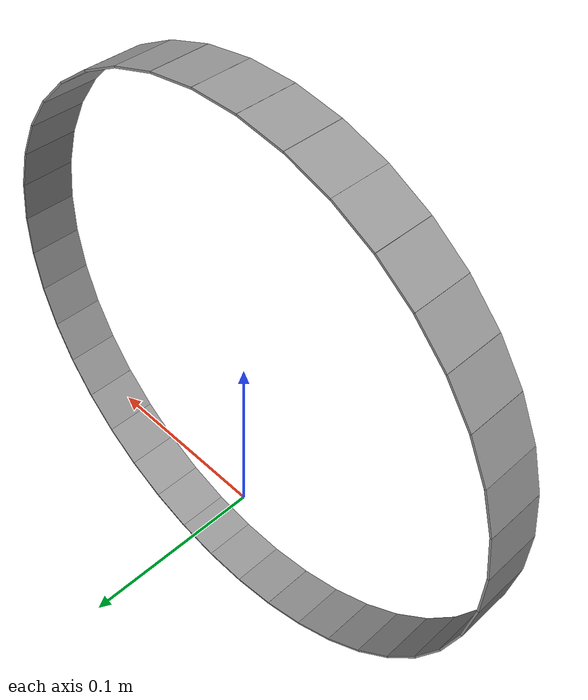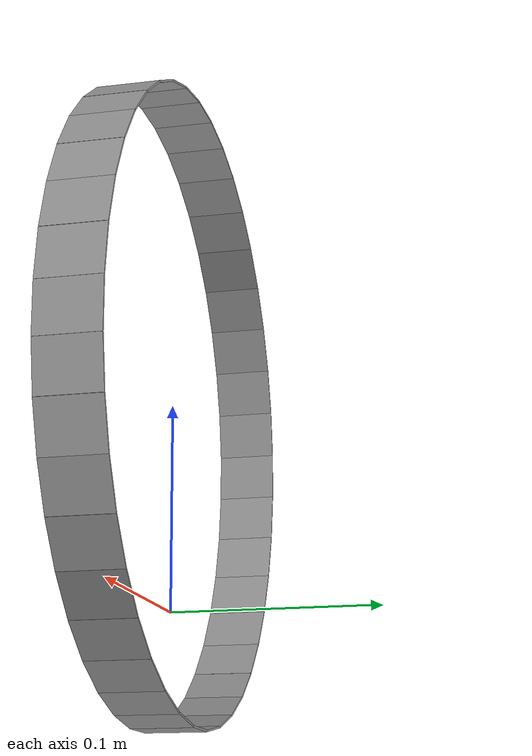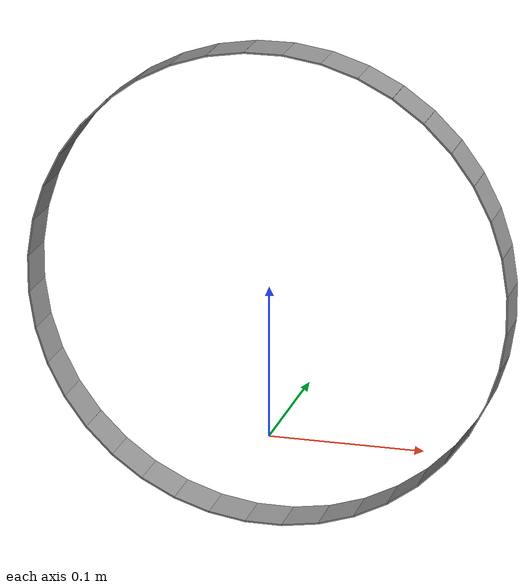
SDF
<sdf version="1.5">
<model name="track">
<static>0</static>
<allow_auto_disable>1</allow_auto_disable>
<pose frame="">0 0 0.1 1.57 0 0</pose>
<link name="link_0">
  <pose frame="">0.1536 0.0000 0.0000 -1.5708 0.0000 1.5708 </pose>
  <inertial>
    <mass>0.1</mass>
    <inertia>
      <ixx>0.166667</ixx>
      <ixy>0</ixy>
      <ixz>0</ixz>
      <iyy>0.166667</iyy>
      <iyz>0</iyz>
      <izz>0.166667</izz>
    </inertia>
    <pose frame="">0 0 0 0 -0 0</pose>
  </inertial>
  <self_collide>0</self_collide>
  <kinematic>0</kinematic>
  <gravity>1</gravity>
  <visual name="visual">
    <pose frame="">0 0 0 0 -0 0</pose>
    <geometry>
       <box>
         <size>0.024178 0.03 0.001</size>
       </box>
    </geometry>
    <material>
      <lighting>1</lighting>
      <script>
        <uri>file://media/materials/scripts/gazebo.material</uri>
        <name>Gazebo/Grey</name>
      </script>
      <ambient>0.3 0.3 0.3 1</ambient>
      <diffuse>0.7 0.7 0.7 1</diffuse>
      <specular>0.01 0.01 0.01 1</specular>
      <emissive>0 0 0 1</emissive>
      <shader type="vertex">
        <normal_map>__default__</normal_map>
      </shader>
    </material>
    <cast_shadows>1</cast_shadows>
    <transparency>0</transparency>
  </visual>
  <collision name="collision">
    <laser_retro>0</laser_retro>
    <max_contacts>10</max_contacts>
    <pose frame="">0 0 0 0 -0 0</pose>
    <geometry>
      <box>
         <size>0.024178 0.03 0.008</size>
       </box>
    </geometry>
    <surface>
      <friction>
        <ode>
          <mu>1</mu>
          <mu2>1</mu2>
          <fdir1>1 0 0</fdir1>
          <slip1>0</slip1>
          <slip2>0</slip2>
        </ode>
      </friction>
      <bounce>
        <restitution_coefficient>0</restitution_coefficient>
        <threshold>1</threshold>
      </bounce>
      <contact>
        <collide_without_contact>0</collide_without_contact>
        <collide_without_contact_bitmask>1</collide_without_contact_bitmask>
        <collide_bitmask>1</collide_bitmask>
        <ode>
          <soft_cfm>0.1</soft_cfm>
          <soft_erp>0.2</soft_erp>
          <kp>1e+13</kp>
          <kd>1</kd>
          <max_vel>0.01</max_vel>
          <min_depth>0</min_depth>
        </ode>
        <bullet>
          <split_impulse>1</split_impulse>
          <split_impulse_penetration_threshold>-0.01</split_impulse_penetration_threshold>
          <soft_cfm>0</soft_cfm>
          <soft_erp>0.2</soft_erp>
          <kp>1e+13</kp>
          <kd>1</kd>
        </bullet>
      </contact>
      </surface>
  </collision>
</link><link name="link_1">
  <pose frame="">0.1517 0.0240 0.0000 -1.5708 0.0000 1.7279 </pose>
  <inertial>
    <mass>0.1</mass>
    <inertia>
      <ixx>0.166667</ixx>
      <ixy>0</ixy>
      <ixz>0</ixz>
      <iyy>0.166667</iyy>
      <iyz>0</iyz>
      <izz>0.166667</izz>
    </inertia>
    <pose frame="">0 0 0 0 -0 0</pose>
  </inertial>
  <self_collide>0</self_collide>
  <kinematic>0</kinematic>
  <gravity>1</gravity>
  <visual name="visual">
    <pose frame="">0 0 0 0 -0 0</pose>
    <geometry>
       <box>
         <size>0.024178 0.03 0.001</size>
       </box>
    </geometry>
    <material>
      <lighting>1</lighting>
      <script>
        <uri>file://media/materials/scripts/gazebo.material</uri>
        <name>Gazebo/Grey</name>
      </script>
      <ambient>0.3 0.3 0.3 1</ambient>
      <diffuse>0.7 0.7 0.7 1</diffuse>
      <specular>0.01 0.01 0.01 1</specular>
      <emissive>0 0 0 1</emissive>
      <shader type="vertex">
        <normal_map>__default__</normal_map>
      </shader>
    </material>
    <cast_shadows>1</cast_shadows>
    <transparency>0</transparency>
  </visual>
  <collision name="collision">
    <laser_retro>0</laser_retro>
    <max_contacts>10</max_contacts>
    <pose frame="">0 0 0 0 -0 0</pose>
    <geometry>
      <box>
         <size>0.024178 0.03 0.008</size>
       </box>
    </geometry>
    <surface>
      <friction>
        <ode>
          <mu>1</mu>
          <mu2>1</mu2>
          <fdir1>1 0 0</fdir1>
          <slip1>0</slip1>
          <slip2>0</slip2>
        </ode>
      </friction>
      <bounce>
        <restitution_coefficient>0</restitution_coefficient>
        <threshold>1</threshold>
      </bounce>
      <contact>
        <collide_without_contact>0</collide_without_contact>
        <collide_without_contact_bitmask>1</collide_without_contact_bitmask>
        <collide_bitmask>1</collide_bitmask>
        <ode>
          <soft_cfm>0.1</soft_cfm>
          <soft_erp>0.2</soft_erp>
          <kp>1e+13</kp>
          <kd>1</kd>
          <max_vel>0.01</max_vel>
          <min_depth>0</min_depth>
        </ode>
        <bullet>
          <split_impulse>1</split_impulse>
          <split_impulse_penetration_threshold>-0.01</split_impulse_penetration_threshold>
          <soft_cfm>0</soft_cfm>
          <soft_erp>0.2</soft_erp>
          <kp>1e+13</kp>
          <kd>1</kd>
        </bullet>
      </contact>
      </surface>
  </collision>
</link><link name="link_2">
  <pose frame="">0.1461 0.0475 0.0000 -1.5708 0.0000 1.8850 </pose>
  <inertial>
    <mass>0.1</mass>
    <inertia>
      <ixx>0.166667</ixx>
      <ixy>0</ixy>
      <ixz>0</ixz>
      <iyy>0.166667</iyy>
      <iyz>0</iyz>
      <izz>0.166667</izz>
    </inertia>
    <pose frame="">0 0 0 0 -0 0</pose>
  </inertial>
  <self_collide>0</self_collide>
  <kinematic>0</kinematic>
  <gravity>1</gravity>
  <visual name="visual">
    <pose frame="">0 0 0 0 -0 0</pose>
    <geometry>
       <box>
         <size>0.024178 0.03 0.001</size>
       </box>
    </geometry>
    <material>
      <lighting>1</lighting>
      <script>
        <uri>file://media/materials/scripts/gazebo.material</uri>
        <name>Gazebo/Grey</name>
      </script>
      <ambient>0.3 0.3 0.3 1</ambient>
      <diffuse>0.7 0.7 0.7 1</diffuse>
      <specular>0.01 0.01 0.01 1</specular>
      <emissive>0 0 0 1</emissive>
      <shader type="vertex">
        <normal_map>__default__</normal_map>
      </shader>
    </material>
    <cast_shadows>1</cast_shadows>
    <transparency>0</transparency>
  </visual>
  <collision name="collision">
    <laser_retro>0</laser_retro>
    <max_contacts>10</max_contacts>
    <pose frame="">0 0 0 0 -0 0</pose>
    <geometry>
      <box>
         <size>0.024178 0.03 0.008</size>
       </box>
    </geometry>
    <surface>
      <friction>
        <ode>
          <mu>1</mu>
          <mu2>1</mu2>
          <fdir1>1 0 0</fdir1>
          <slip1>0</slip1>
          <slip2>0</slip2>
        </ode>
      </friction>
      <bounce>
        <restitution_coefficient>0</restitution_coefficient>
        <threshold>1</threshold>
      </bounce>
      <contact>
        <collide_without_contact>0</collide_without_contact>
        <collide_without_contact_bitmask>1</collide_without_contact_bitmask>
        <collide_bitmask>1</collide_bitmask>
        <ode>
          <soft_cfm>0.1</soft_cfm>
          <soft_erp>0.2</soft_erp>
          <kp>1e+13</kp>
          <kd>1</kd>
          <max_vel>0.01</max_vel>
          <min_depth>0</min_depth>
        </ode>
        <bullet>
          <split_impulse>1</split_impulse>
          <split_impulse_penetration_threshold>-0.01</split_impulse_penetration_threshold>
          <soft_cfm>0</soft_cfm>
          <soft_erp>0.2</soft_erp>
          <kp>1e+13</kp>
          <kd>1</kd>
        </bullet>
      </contact>
      </surface>
  </collision>
</link><link name="link_3">
  <pose frame="">0.1369 0.0697 0.0000 -1.5708 0.0000 2.0420 </pose>
  <inertial>
    <mass>0.1</mass>
    <inertia>
      <ixx>0.166667</ixx>
      <ixy>0</ixy>
      <ixz>0</ixz>
      <iyy>0.166667</iyy>
      <iyz>0</iyz>
      <izz>0.166667</izz>
    </inertia>
    <pose frame="">0 0 0 0 -0 0</pose>
  </inertial>
  <self_collide>0</self_collide>
  <kinematic>0</kinematic>
  <gravity>1</gravity>
  <visual name="visual">
    <pose frame="">0 0 0 0 -0 0</pose>
    <geometry>
       <box>
         <size>0.024178 0.03 0.001</size>
       </box>
    </geometry>
    <material>
      <lighting>1</lighting>
      <script>
        <uri>file://media/materials/scripts/gazebo.material</uri>
        <name>Gazebo/Grey</name>
      </script>
      <ambient>0.3 0.3 0.3 1</ambient>
      <diffuse>0.7 0.7 0.7 1</diffuse>
      <specular>0.01 0.01 0.01 1</specular>
      <emissive>0 0 0 1</emissive>
      <shader type="vertex">
        <normal_map>__default__</normal_map>
      </shader>
    </material>
    <cast_shadows>1</cast_shadows>
    <transparency>0</transparency>
  </visual>
  <collision name="collision">
    <laser_retro>0</laser_retro>
    <max_contacts>10</max_contacts>
    <pose frame="">0 0 0 0 -0 0</pose>
    <geometry>
      <box>
         <size>0.024178 0.03 0.008</size>
       </box>
    </geometry>
    <surface>
      <friction>
        <ode>
          <mu>1</mu>
          <mu2>1</mu2>
          <fdir1>1 0 0</fdir1>
          <slip1>0</slip1>
          <slip2>0</slip2>
        </ode>
      </friction>
      <bounce>
        <restitution_coefficient>0</restitution_coefficient>
        <threshold>1</threshold>
      </bounce>
      <contact>
        <collide_without_contact>0</collide_without_contact>
        <collide_without_contact_bitmask>1</collide_without_contact_bitmask>
        <collide_bitmask>1</collide_bitmask>
        <ode>
          <soft_cfm>0.1</soft_cfm>
          <soft_erp>0.2</soft_erp>
          <kp>1e+13</kp>
          <kd>1</kd>
          <max_vel>0.01</max_vel>
          <min_depth>0</min_depth>
        </ode>
        <bullet>
          <split_impulse>1</split_impulse>
          <split_impulse_penetration_threshold>-0.01</split_impulse_penetration_threshold>
          <soft_cfm>0</soft_cfm>
          <soft_erp>0.2</soft_erp>
          <kp>1e+13</kp>
          <kd>1</kd>
        </bullet>
      </contact>
      </surface>
  </collision>
</link><link name="link_4">
  <pose frame="">0.1243 0.0903 0.0000 -1.5708 0.0000 2.1991 </pose>
  <inertial>
    <mass>0.1</mass>
    <inertia>
      <ixx>0.166667</ixx>
      <ixy>0</ixy>
      <ixz>0</ixz>
      <iyy>0.166667</iyy>
      <iyz>0</iyz>
      <izz>0.166667</izz>
    </inertia>
    <pose frame="">0 0 0 0 -0 0</pose>
  </inertial>
  <self_collide>0</self_collide>
  <kinematic>0</kinematic>
  <gravity>1</gravity>
  <visual name="visual">
    <pose frame="">0 0 0 0 -0 0</pose>
    <geometry>
       <box>
         <size>0.024178 0.03 0.001</size>
       </box>
    </geometry>
    <material>
      <lighting>1</lighting>
      <script>
        <uri>file://media/materials/scripts/gazebo.material</uri>
        <name>Gazebo/Grey</name>
      </script>
      <ambient>0.3 0.3 0.3 1</ambient>
      <diffuse>0.7 0.7 0.7 1</diffuse>
      <specular>0.01 0.01 0.01 1</specular>
      <emissive>0 0 0 1</emissive>
      <shader type="vertex">
        <normal_map>__default__</normal_map>
      </shader>
    </material>
    <cast_shadows>1</cast_shadows>
    <transparency>0</transparency>
  </visual>
  <collision name="collision">
    <laser_retro>0</laser_retro>
    <max_contacts>10</max_contacts>
    <pose frame="">0 0 0 0 -0 0</pose>
    <geometry>
      <box>
         <size>0.024178 0.03 0.008</size>
       </box>
    </geometry>
    <surface>
      <friction>
        <ode>
          <mu>1</mu>
          <mu2>1</mu2>
          <fdir1>1 0 0</fdir1>
          <slip1>0</slip1>
          <slip2>0</slip2>
        </ode>
      </friction>
      <bounce>
        <restitution_coefficient>0</restitution_coefficient>
        <threshold>1</threshold>
      </bounce>
      <contact>
        <collide_without_contact>0</collide_without_contact>
        <collide_without_contact_bitmask>1</collide_without_contact_bitmask>
        <collide_bitmask>1</collide_bitmask>
        <ode>
          <soft_cfm>0.1</soft_cfm>
          <soft_erp>0.2</soft_erp>
          <kp>1e+13</kp>
          <kd>1</kd>
          <max_vel>0.01</max_vel>
          <min_depth>0</min_depth>
        </ode>
        <bullet>
          <split_impulse>1</split_impulse>
          <split_impulse_penetration_threshold>-0.01</split_impulse_penetration_threshold>
          <soft_cfm>0</soft_cfm>
          <soft_erp>0.2</soft_erp>
          <kp>1e+13</kp>
          <kd>1</kd>
        </bullet>
      </contact>
      </surface>
  </collision>
</link><link name="link_5">
  <pose frame="">0.1086 0.1086 0.0000 -1.5708 0.0000 2.3562 </pose>
  <inertial>
    <mass>0.1</mass>
    <inertia>
      <ixx>0.166667</ixx>
      <ixy>0</ixy>
      <ixz>0</ixz>
      <iyy>0.166667</iyy>
      <iyz>0</iyz>
      <izz>0.166667</izz>
    </inertia>
    <pose frame="">0 0 0 0 -0 0</pose>
  </inertial>
  <self_collide>0</self_collide>
  <kinematic>0</kinematic>
  <gravity>1</gravity>
  <visual name="visual">
    <pose frame="">0 0 0 0 -0 0</pose>
    <geometry>
       <box>
         <size>0.024178 0.03 0.001</size>
       </box>
    </geometry>
    <material>
      <lighting>1</lighting>
      <script>
        <uri>file://media/materials/scripts/gazebo.material</uri>
        <name>Gazebo/Grey</name>
      </script>
      <ambient>0.3 0.3 0.3 1</ambient>
      <diffuse>0.7 0.7 0.7 1</diffuse>
      <specular>0.01 0.01 0.01 1</specular>
      <emissive>0 0 0 1</emissive>
      <shader type="vertex">
        <normal_map>__default__</normal_map>
      </shader>
    </material>
    <cast_shadows>1</cast_shadows>
    <transparency>0</transparency>
  </visual>
  <collision name="collision">
    <laser_retro>0</laser_retro>
    <max_contacts>10</max_contacts>
    <pose frame="">0 0 0 0 -0 0</pose>
    <geometry>
      <box>
         <size>0.024178 0.03 0.008</size>
       </box>
    </geometry>
    <surface>
      <friction>
        <ode>
          <mu>1</mu>
          <mu2>1</mu2>
          <fdir1>1 0 0</fdir1>
          <slip1>0</slip1>
          <slip2>0</slip2>
        </ode>
      </friction>
      <bounce>
        <restitution_coefficient>0</restitution_coefficient>
        <threshold>1</threshold>
      </bounce>
      <contact>
        <collide_without_contact>0</collide_without_contact>
        <collide_without_contact_bitmask>1</collide_without_contact_bitmask>
        <collide_bitmask>1</collide_bitmask>
        <ode>
          <soft_cfm>0.1</soft_cfm>
          <soft_erp>0.2</soft_erp>
          <kp>1e+13</kp>
          <kd>1</kd>
          <max_vel>0.01</max_vel>
          <min_depth>0</min_depth>
        </ode>
        <bullet>
          <split_impulse>1</split_impulse>
          <split_impulse_penetration_threshold>-0.01</split_impulse_penetration_threshold>
          <soft_cfm>0</soft_cfm>
          <soft_erp>0.2</soft_erp>
          <kp>1e+13</kp>
          <kd>1</kd>
        </bullet>
      </contact>
      </surface>
  </collision>
</link><link name="link_6">
  <pose frame="">0.0903 0.1243 0.0000 -1.5708 0.0000 2.5133 </pose>
  <inertial>
    <mass>0.1</mass>
    <inertia>
      <ixx>0.166667</ixx>
      <ixy>0</ixy>
      <ixz>0</ixz>
      <iyy>0.166667</iyy>
      <iyz>0</iyz>
      <izz>0.166667</izz>
    </inertia>
    <pose frame="">0 0 0 0 -0 0</pose>
  </inertial>
  <self_collide>0</self_collide>
  <kinematic>0</kinematic>
  <gravity>1</gravity>
  <visual name="visual">
    <pose frame="">0 0 0 0 -0 0</pose>
    <geometry>
       <box>
         <size>0.024178 0.03 0.001</size>
       </box>
    </geometry>
    <material>
      <lighting>1</lighting>
      <script>
        <uri>file://media/materials/scripts/gazebo.material</uri>
        <name>Gazebo/Grey</name>
      </script>
      <ambient>0.3 0.3 0.3 1</ambient>
      <diffuse>0.7 0.7 0.7 1</diffuse>
      <specular>0.01 0.01 0.01 1</specular>
      <emissive>0 0 0 1</emissive>
      <shader type="vertex">
        <normal_map>__default__</normal_map>
      </shader>
    </material>
    <cast_shadows>1</cast_shadows>
    <transparency>0</transparency>
  </visual>
  <collision name="collision">
    <laser_retro>0</laser_retro>
    <max_contacts>10</max_contacts>
    <pose frame="">0 0 0 0 -0 0</pose>
    <geometry>
      <box>
         <size>0.024178 0.03 0.008</size>
       </box>
    </geometry>
    <surface>
      <friction>
        <ode>
          <mu>1</mu>
          <mu2>1</mu2>
          <fdir1>1 0 0</fdir1>
          <slip1>0</slip1>
          <slip2>0</slip2>
        </ode>
      </friction>
      <bounce>
        <restitution_coefficient>0</restitution_coefficient>
        <threshold>1</threshold>
      </bounce>
      <contact>
        <collide_without_contact>0</collide_without_contact>
        <collide_without_contact_bitmask>1</collide_without_contact_bitmask>
        <collide_bitmask>1</collide_bitmask>
        <ode>
          <soft_cfm>0.1</soft_cfm>
          <soft_erp>0.2</soft_erp>
          <kp>1e+13</kp>
          <kd>1</kd>
          <max_vel>0.01</max_vel>
          <min_depth>0</min_depth>
        </ode>
        <bullet>
          <split_impulse>1</split_impulse>
          <split_impulse_penetration_threshold>-0.01</split_impulse_penetration_threshold>
          <soft_cfm>0</soft_cfm>
          <soft_erp>0.2</soft_erp>
          <kp>1e+13</kp>
          <kd>1</kd>
        </bullet>
      </contact>
      </surface>
  </collision>
</link><link name="link_7">
  <pose frame="">0.0697 0.1369 0.0000 -1.5708 0.0000 2.6704 </pose>
  <inertial>
    <mass>0.1</mass>
    <inertia>
      <ixx>0.166667</ixx>
      <ixy>0</ixy>
      <ixz>0</ixz>
      <iyy>0.166667</iyy>
      <iyz>0</iyz>
      <izz>0.166667</izz>
    </inertia>
    <pose frame="">0 0 0 0 -0 0</pose>
  </inertial>
  <self_collide>0</self_collide>
  <kinematic>0</kinematic>
  <gravity>1</gravity>
  <visual name="visual">
    <pose frame="">0 0 0 0 -0 0</pose>
    <geometry>
       <box>
         <size>0.024178 0.03 0.001</size>
       </box>
    </geometry>
    <material>
      <lighting>1</lighting>
      <script>
        <uri>file://media/materials/scripts/gazebo.material</uri>
        <name>Gazebo/Grey</name>
      </script>
      <ambient>0.3 0.3 0.3 1</ambient>
      <diffuse>0.7 0.7 0.7 1</diffuse>
      <specular>0.01 0.01 0.01 1</specular>
      <emissive>0 0 0 1</emissive>
      <shader type="vertex">
        <normal_map>__default__</normal_map>
      </shader>
    </material>
    <cast_shadows>1</cast_shadows>
    <transparency>0</transparency>
  </visual>
  <collision name="collision">
    <laser_retro>0</laser_retro>
    <max_contacts>10</max_contacts>
    <pose frame="">0 0 0 0 -0 0</pose>
    <geometry>
      <box>
         <size>0.024178 0.03 0.008</size>
       </box>
    </geometry>
    <surface>
      <friction>
        <ode>
          <mu>1</mu>
          <mu2>1</mu2>
          <fdir1>1 0 0</fdir1>
          <slip1>0</slip1>
          <slip2>0</slip2>
        </ode>
      </friction>
      <bounce>
        <restitution_coefficient>0</restitution_coefficient>
        <threshold>1</threshold>
      </bounce>
      <contact>
        <collide_without_contact>0</collide_without_contact>
        <collide_without_contact_bitmask>1</collide_without_contact_bitmask>
        <collide_bitmask>1</collide_bitmask>
        <ode>
          <soft_cfm>0.1</soft_cfm>
          <soft_erp>0.2</soft_erp>
          <kp>1e+13</kp>
          <kd>1</kd>
          <max_vel>0.01</max_vel>
          <min_depth>0</min_depth>
        </ode>
        <bullet>
          <split_impulse>1</split_impulse>
          <split_impulse_penetration_threshold>-0.01</split_impulse_penetration_threshold>
          <soft_cfm>0</soft_cfm>
          <soft_erp>0.2</soft_erp>
          <kp>1e+13</kp>
          <kd>1</kd>
        </bullet>
      </contact>
      </surface>
  </collision>
</link><link name="link_8">
  <pose frame="">0.0475 0.1461 0.0000 -1.5708 0.0000 2.8274 </pose>
  <inertial>
    <mass>0.1</mass>
    <inertia>
      <ixx>0.166667</ixx>
      <ixy>0</ixy>
      <ixz>0</ixz>
      <iyy>0.166667</iyy>
      <iyz>0</iyz>
      <izz>0.166667</izz>
    </inertia>
    <pose frame="">0 0 0 0 -0 0</pose>
  </inertial>
  <self_collide>0</self_collide>
  <kinematic>0</kinematic>
  <gravity>1</gravity>
  <visual name="visual">
    <pose frame="">0 0 0 0 -0 0</pose>
    <geometry>
       <box>
         <size>0.024178 0.03 0.001</size>
       </box>
    </geometry>
    <material>
      <lighting>1</lighting>
      <script>
        <uri>file://media/materials/scripts/gazebo.material</uri>
        <name>Gazebo/Grey</name>
      </script>
      <ambient>0.3 0.3 0.3 1</ambient>
      <diffuse>0.7 0.7 0.7 1</diffuse>
      <specular>0.01 0.01 0.01 1</specular>
      <emissive>0 0 0 1</emissive>
      <shader type="vertex">
        <normal_map>__default__</normal_map>
      </shader>
    </material>
    <cast_shadows>1</cast_shadows>
    <transparency>0</transparency>
  </visual>
  <collision name="collision">
    <laser_retro>0</laser_retro>
    <max_contacts>10</max_contacts>
    <pose frame="">0 0 0 0 -0 0</pose>
    <geometry>
      <box>
         <size>0.024178 0.03 0.008</size>
       </box>
    </geometry>
    <surface>
      <friction>
        <ode>
          <mu>1</mu>
          <mu2>1</mu2>
          <fdir1>1 0 0</fdir1>
          <slip1>0</slip1>
          <slip2>0</slip2>
        </ode>
      </friction>
      <bounce>
        <restitution_coefficient>0</restitution_coefficient>
        <threshold>1</threshold>
      </bounce>
      <contact>
        <collide_without_contact>0</collide_without_contact>
        <collide_without_contact_bitmask>1</collide_without_contact_bitmask>
        <collide_bitmask>1</collide_bitmask>
        <ode>
          <soft_cfm>0.1</soft_cfm>
          <soft_erp>0.2</soft_erp>
          <kp>1e+13</kp>
          <kd>1</kd>
          <max_vel>0.01</max_vel>
          <min_depth>0</min_depth>
        </ode>
        <bullet>
          <split_impulse>1</split_impulse>
          <split_impulse_penetration_threshold>-0.01</split_impulse_penetration_threshold>
          <soft_cfm>0</soft_cfm>
          <soft_erp>0.2</soft_erp>
          <kp>1e+13</kp>
          <kd>1</kd>
        </bullet>
      </contact>
      </surface>
  </collision>
</link><link name="link_9">
  <pose frame="">0.0240 0.1517 0.0000 -1.5708 0.0000 2.9845 </pose>
  <inertial>
    <mass>0.1</mass>
    <inertia>
      <ixx>0.166667</ixx>
      <ixy>0</ixy>
      <ixz>0</ixz>
      <iyy>0.166667</iyy>
      <iyz>0</iyz>
      <izz>0.166667</izz>
    </inertia>
    <pose frame="">0 0 0 0 -0 0</pose>
  </inertial>
  <self_collide>0</self_collide>
  <kinematic>0</kinematic>
  <gravity>1</gravity>
  <visual name="visual">
    <pose frame="">0 0 0 0 -0 0</pose>
    <geometry>
       <box>
         <size>0.024178 0.03 0.001</size>
       </box>
    </geometry>
    <material>
      <lighting>1</lighting>
      <script>
        <uri>file://media/materials/scripts/gazebo.material</uri>
        <name>Gazebo/Grey</name>
      </script>
      <ambient>0.3 0.3 0.3 1</ambient>
      <diffuse>0.7 0.7 0.7 1</diffuse>
      <specular>0.01 0.01 0.01 1</specular>
      <emissive>0 0 0 1</emissive>
      <shader type="vertex">
        <normal_map>__default__</normal_map>
      </shader>
    </material>
    <cast_shadows>1</cast_shadows>
    <transparency>0</transparency>
  </visual>
  <collision name="collision">
    <laser_retro>0</laser_retro>
    <max_contacts>10</max_contacts>
    <pose frame="">0 0 0 0 -0 0</pose>
    <geometry>
      <box>
         <size>0.024178 0.03 0.008</size>
       </box>
    </geometry>
    <surface>
      <friction>
        <ode>
          <mu>1</mu>
          <mu2>1</mu2>
          <fdir1>1 0 0</fdir1>
          <slip1>0</slip1>
          <slip2>0</slip2>
        </ode>
      </friction>
      <bounce>
        <restitution_coefficient>0</restitution_coefficient>
        <threshold>1</threshold>
      </bounce>
      <contact>
        <collide_without_contact>0</collide_without_contact>
        <collide_without_contact_bitmask>1</collide_without_contact_bitmask>
        <collide_bitmask>1</collide_bitmask>
        <ode>
          <soft_cfm>0.1</soft_cfm>
          <soft_erp>0.2</soft_erp>
          <kp>1e+13</kp>
          <kd>1</kd>
          <max_vel>0.01</max_vel>
          <min_depth>0</min_depth>
        </ode>
        <bullet>
          <split_impulse>1</split_impulse>
          <split_impulse_penetration_threshold>-0.01</split_impulse_penetration_threshold>
          <soft_cfm>0</soft_cfm>
          <soft_erp>0.2</soft_erp>
          <kp>1e+13</kp>
          <kd>1</kd>
        </bullet>
      </contact>
      </surface>
  </collision>
</link><link name="link_10">
  <pose frame="">0.0000 0.1536 0.0000 -1.5708 0.0000 3.1416 </pose>
  <inertial>
    <mass>0.1</mass>
    <inertia>
      <ixx>0.166667</ixx>
      <ixy>0</ixy>
      <ixz>0</ixz>
      <iyy>0.166667</iyy>
      <iyz>0</iyz>
      <izz>0.166667</izz>
    </inertia>
    <pose frame="">0 0 0 0 -0 0</pose>
  </inertial>
  <self_collide>0</self_collide>
  <kinematic>0</kinematic>
  <gravity>1</gravity>
  <visual name="visual">
    <pose frame="">0 0 0 0 -0 0</pose>
    <geometry>
       <box>
         <size>0.024178 0.03 0.001</size>
       </box>
    </geometry>
    <material>
      <lighting>1</lighting>
      <script>
        <uri>file://media/materials/scripts/gazebo.material</uri>
        <name>Gazebo/Grey</name>
      </script>
      <ambient>0.3 0.3 0.3 1</ambient>
      <diffuse>0.7 0.7 0.7 1</diffuse>
      <specular>0.01 0.01 0.01 1</specular>
      <emissive>0 0 0 1</emissive>
      <shader type="vertex">
        <normal_map>__default__</normal_map>
      </shader>
    </material>
    <cast_shadows>1</cast_shadows>
    <transparency>0</transparency>
  </visual>
  <collision name="collision">
    <laser_retro>0</laser_retro>
    <max_contacts>10</max_contacts>
    <pose frame="">0 0 0 0 -0 0</pose>
    <geometry>
      <box>
         <size>0.024178 0.03 0.008</size>
       </box>
    </geometry>
    <surface>
      <friction>
        <ode>
          <mu>1</mu>
          <mu2>1</mu2>
          <fdir1>1 0 0</fdir1>
          <slip1>0</slip1>
          <slip2>0</slip2>
        </ode>
      </friction>
      <bounce>
        <restitution_coefficient>0</restitution_coefficient>
        <threshold>1</threshold>
      </bounce>
      <contact>
        <collide_without_contact>0</collide_without_contact>
        <collide_without_contact_bitmask>1</collide_without_contact_bitmask>
        <collide_bitmask>1</collide_bitmask>
        <ode>
          <soft_cfm>0.1</soft_cfm>
          <soft_erp>0.2</soft_erp>
          <kp>1e+13</kp>
          <kd>1</kd>
          <max_vel>0.01</max_vel>
          <min_depth>0</min_depth>
        </ode>
        <bullet>
          <split_impulse>1</split_impulse>
          <split_impulse_penetration_threshold>-0.01</split_impulse_penetration_threshold>
          <soft_cfm>0</soft_cfm>
          <soft_erp>0.2</soft_erp>
          <kp>1e+13</kp>
          <kd>1</kd>
        </bullet>
      </contact>
      </surface>
  </collision>
</link><link name="link_11">
  <pose frame="">-0.0240 0.1517 0.0000 -1.5708 0.0000 3.2987 </pose>
  <inertial>
    <mass>0.1</mass>
    <inertia>
      <ixx>0.166667</ixx>
      <ixy>0</ixy>
      <ixz>0</ixz>
      <iyy>0.166667</iyy>
      <iyz>0</iyz>
      <izz>0.166667</izz>
    </inertia>
    <pose frame="">0 0 0 0 -0 0</pose>
  </inertial>
  <self_collide>0</self_collide>
  <kinematic>0</kinematic>
  <gravity>1</gravity>
  <visual name="visual">
    <pose frame="">0 0 0 0 -0 0</pose>
    <geometry>
       <box>
         <size>0.024178 0.03 0.001</size>
       </box>
    </geometry>
    <material>
      <lighting>1</lighting>
      <script>
        <uri>file://media/materials/scripts/gazebo.material</uri>
        <name>Gazebo/Grey</name>
      </script>
      <ambient>0.3 0.3 0.3 1</ambient>
      <diffuse>0.7 0.7 0.7 1</diffuse>
      <specular>0.01 0.01 0.01 1</specular>
      <emissive>0 0 0 1</emissive>
      <shader type="vertex">
        <normal_map>__default__</normal_map>
      </shader>
    </material>
    <cast_shadows>1</cast_shadows>
    <transparency>0</transparency>
  </visual>
  <collision name="collision">
    <laser_retro>0</laser_retro>
    <max_contacts>10</max_contacts>
    <pose frame="">0 0 0 0 -0 0</pose>
    <geometry>
      <box>
         <size>0.024178 0.03 0.008</size>
       </box>
    </geometry>
    <surface>
      <friction>
        <ode>
          <mu>1</mu>
          <mu2>1</mu2>
          <fdir1>1 0 0</fdir1>
          <slip1>0</slip1>
          <slip2>0</slip2>
        </ode>
      </friction>
      <bounce>
        <restitution_coefficient>0</restitution_coefficient>
        <threshold>1</threshold>
      </bounce>
      <contact>
        <collide_without_contact>0</collide_without_contact>
        <collide_without_contact_bitmask>1</collide_without_contact_bitmask>
        <collide_bitmask>1</collide_bitmask>
        <ode>
          <soft_cfm>0.1</soft_cfm>
          <soft_erp>0.2</soft_erp>
          <kp>1e+13</kp>
          <kd>1</kd>
          <max_vel>0.01</max_vel>
          <min_depth>0</min_depth>
        </ode>
        <bullet>
          <split_impulse>1</split_impulse>
          <split_impulse_penetration_threshold>-0.01</split_impulse_penetration_threshold>
          <soft_cfm>0</soft_cfm>
          <soft_erp>0.2</soft_erp>
          <kp>1e+13</kp>
          <kd>1</kd>
        </bullet>
      </contact>
      </surface>
  </collision>
</link><link name="link_12">
  <pose frame="">-0.0475 0.1461 0.0000 -1.5708 0.0000 3.4558 </pose>
  <inertial>
    <mass>0.1</mass>
    <inertia>
      <ixx>0.166667</ixx>
      <ixy>0</ixy>
      <ixz>0</ixz>
      <iyy>0.166667</iyy>
      <iyz>0</iyz>
      <izz>0.166667</izz>
    </inertia>
    <pose frame="">0 0 0 0 -0 0</pose>
  </inertial>
  <self_collide>0</self_collide>
  <kinematic>0</kinematic>
  <gravity>1</gravity>
  <visual name="visual">
    <pose frame="">0 0 0 0 -0 0</pose>
    <geometry>
       <box>
         <size>0.024178 0.03 0.001</size>
       </box>
    </geometry>
    <material>
      <lighting>1</lighting>
      <script>
        <uri>file://media/materials/scripts/gazebo.material</uri>
        <name>Gazebo/Grey</name>
      </script>
      <ambient>0.3 0.3 0.3 1</ambient>
      <diffuse>0.7 0.7 0.7 1</diffuse>
      <specular>0.01 0.01 0.01 1</specular>
      <emissive>0 0 0 1</emissive>
      <shader type="vertex">
        <normal_map>__default__</normal_map>
      </shader>
    </material>
    <cast_shadows>1</cast_shadows>
    <transparency>0</transparency>
  </visual>
  <collision name="collision">
    <laser_retro>0</laser_retro>
    <max_contacts>10</max_contacts>
    <pose frame="">0 0 0 0 -0 0</pose>
    <geometry>
      <box>
         <size>0.024178 0.03 0.008</size>
       </box>
    </geometry>
    <surface>
      <friction>
        <ode>
          <mu>1</mu>
          <mu2>1</mu2>
          <fdir1>1 0 0</fdir1>
          <slip1>0</slip1>
          <slip2>0</slip2>
        </ode>
      </friction>
      <bounce>
        <restitution_coefficient>0</restitution_coefficient>
        <threshold>1</threshold>
      </bounce>
      <contact>
        <collide_without_contact>0</collide_without_contact>
        <collide_without_contact_bitmask>1</collide_without_contact_bitmask>
        <collide_bitmask>1</collide_bitmask>
        <ode>
          <soft_cfm>0.1</soft_cfm>
          <soft_erp>0.2</soft_erp>
          <kp>1e+13</kp>
          <kd>1</kd>
          <max_vel>0.01</max_vel>
          <min_depth>0</min_depth>
        </ode>
        <bullet>
          <split_impulse>1</split_impulse>
          <split_impulse_penetration_threshold>-0.01</split_impulse_penetration_threshold>
          <soft_cfm>0</soft_cfm>
          <soft_erp>0.2</soft_erp>
          <kp>1e+13</kp>
          <kd>1</kd>
        </bullet>
      </contact>
      </surface>
  </collision>
</link><link name="link_13">
  <pose frame="">-0.0697 0.1369 0.0000 -1.5708 0.0000 3.6128 </pose>
  <inertial>
    <mass>0.1</mass>
    <inertia>
      <ixx>0.166667</ixx>
      <ixy>0</ixy>
      <ixz>0</ixz>
      <iyy>0.166667</iyy>
      <iyz>0</iyz>
      <izz>0.166667</izz>
    </inertia>
    <pose frame="">0 0 0 0 -0 0</pose>
  </inertial>
  <self_collide>0</self_collide>
  <kinematic>0</kinematic>
  <gravity>1</gravity>
  <visual name="visual">
    <pose frame="">0 0 0 0 -0 0</pose>
    <geometry>
       <box>
         <size>0.024178 0.03 0.001</size>
       </box>
    </geometry>
    <material>
      <lighting>1</lighting>
      <script>
        <uri>file://media/materials/scripts/gazebo.material</uri>
        <name>Gazebo/Grey</name>
      </script>
      <ambient>0.3 0.3 0.3 1</ambient>
      <diffuse>0.7 0.7 0.7 1</diffuse>
      <specular>0.01 0.01 0.01 1</specular>
      <emissive>0 0 0 1</emissive>
      <shader type="vertex">
        <normal_map>__default__</normal_map>
      </shader>
    </material>
    <cast_shadows>1</cast_shadows>
    <transparency>0</transparency>
  </visual>
  <collision name="collision">
    <laser_retro>0</laser_retro>
    <max_contacts>10</max_contacts>
    <pose frame="">0 0 0 0 -0 0</pose>
    <geometry>
      <box>
         <size>0.024178 0.03 0.008</size>
       </box>
    </geometry>
    <surface>
      <friction>
        <ode>
          <mu>1</mu>
          <mu2>1</mu2>
          <fdir1>1 0 0</fdir1>
          <slip1>0</slip1>
          <slip2>0</slip2>
        </ode>
      </friction>
      <bounce>
        <restitution_coefficient>0</restitution_coefficient>
        <threshold>1</threshold>
      </bounce>
      <contact>
        <collide_without_contact>0</collide_without_contact>
        <collide_without_contact_bitmask>1</collide_without_contact_bitmask>
        <collide_bitmask>1</collide_bitmask>
        <ode>
          <soft_cfm>0.1</soft_cfm>
          <soft_erp>0.2</soft_erp>
          <kp>1e+13</kp>
          <kd>1</kd>
          <max_vel>0.01</max_vel>
          <min_depth>0</min_depth>
        </ode>
        <bullet>
          <split_impulse>1</split_impulse>
          <split_impulse_penetration_threshold>-0.01</split_impulse_penetration_threshold>
          <soft_cfm>0</soft_cfm>
          <soft_erp>0.2</soft_erp>
          <kp>1e+13</kp>
          <kd>1</kd>
        </bullet>
      </contact>
      </surface>
  </collision>
</link><link name="link_14">
  <pose frame="">-0.0903 0.1243 0.0000 -1.5708 0.0000 3.7699 </pose>
  <inertial>
    <mass>0.1</mass>
    <inertia>
      <ixx>0.166667</ixx>
      <ixy>0</ixy>
      <ixz>0</ixz>
      <iyy>0.166667</iyy>
      <iyz>0</iyz>
      <izz>0.166667</izz>
    </inertia>
    <pose frame="">0 0 0 0 -0 0</pose>
  </inertial>
  <self_collide>0</self_collide>
  <kinematic>0</kinematic>
  <gravity>1</gravity>
  <visual name="visual">
    <pose frame="">0 0 0 0 -0 0</pose>
    <geometry>
       <box>
         <size>0.024178 0.03 0.001</size>
       </box>
    </geometry>
    <material>
      <lighting>1</lighting>
      <script>
        <uri>file://media/materials/scripts/gazebo.material</uri>
        <name>Gazebo/Grey</name>
      </script>
      <ambient>0.3 0.3 0.3 1</ambient>
      <diffuse>0.7 0.7 0.7 1</diffuse>
      <specular>0.01 0.01 0.01 1</specular>
      <emissive>0 0 0 1</emissive>
      <shader type="vertex">
        <normal_map>__default__</normal_map>
      </shader>
    </material>
    <cast_shadows>1</cast_shadows>
    <transparency>0</transparency>
  </visual>
  <collision name="collision">
    <laser_retro>0</laser_retro>
    <max_contacts>10</max_contacts>
    <pose frame="">0 0 0 0 -0 0</pose>
    <geometry>
      <box>
         <size>0.024178 0.03 0.008</size>
       </box>
    </geometry>
    <surface>
      <friction>
        <ode>
          <mu>1</mu>
          <mu2>1</mu2>
          <fdir1>1 0 0</fdir1>
          <slip1>0</slip1>
          <slip2>0</slip2>
        </ode>
      </friction>
      <bounce>
        <restitution_coefficient>0</restitution_coefficient>
        <threshold>1</threshold>
      </bounce>
      <contact>
        <collide_without_contact>0</collide_without_contact>
        <collide_without_contact_bitmask>1</collide_without_contact_bitmask>
        <collide_bitmask>1</collide_bitmask>
        <ode>
          <soft_cfm>0.1</soft_cfm>
          <soft_erp>0.2</soft_erp>
          <kp>1e+13</kp>
          <kd>1</kd>
          <max_vel>0.01</max_vel>
          <min_depth>0</min_depth>
        </ode>
        <bullet>
          <split_impulse>1</split_impulse>
          <split_impulse_penetration_threshold>-0.01</split_impulse_penetration_threshold>
          <soft_cfm>0</soft_cfm>
          <soft_erp>0.2</soft_erp>
          <kp>1e+13</kp>
          <kd>1</kd>
        </bullet>
      </contact>
      </surface>
  </collision>
</link><link name="link_15">
  <pose frame="">-0.1086 0.1086 0.0000 -1.5708 0.0000 3.9270 </pose>
  <inertial>
    <mass>0.1</mass>
    <inertia>
      <ixx>0.166667</ixx>
      <ixy>0</ixy>
      <ixz>0</ixz>
      <iyy>0.166667</iyy>
      <iyz>0</iyz>
      <izz>0.166667</izz>
    </inertia>
    <pose frame="">0 0 0 0 -0 0</pose>
  </inertial>
  <self_collide>0</self_collide>
  <kinematic>0</kinematic>
  <gravity>1</gravity>
  <visual name="visual">
    <pose frame="">0 0 0 0 -0 0</pose>
    <geometry>
       <box>
         <size>0.024178 0.03 0.001</size>
       </box>
    </geometry>
    <material>
      <lighting>1</lighting>
      <script>
        <uri>file://media/materials/scripts/gazebo.material</uri>
        <name>Gazebo/Grey</name>
      </script>
      <ambient>0.3 0.3 0.3 1</ambient>
      <diffuse>0.7 0.7 0.7 1</diffuse>
      <specular>0.01 0.01 0.01 1</specular>
      <emissive>0 0 0 1</emissive>
      <shader type="vertex">
        <normal_map>__default__</normal_map>
      </shader>
    </material>
    <cast_shadows>1</cast_shadows>
    <transparency>0</transparency>
  </visual>
  <collision name="collision">
    <laser_retro>0</laser_retro>
    <max_contacts>10</max_contacts>
    <pose frame="">0 0 0 0 -0 0</pose>
    <geometry>
      <box>
         <size>0.024178 0.03 0.008</size>
       </box>
    </geometry>
    <surface>
      <friction>
        <ode>
          <mu>1</mu>
          <mu2>1</mu2>
          <fdir1>1 0 0</fdir1>
          <slip1>0</slip1>
          <slip2>0</slip2>
        </ode>
      </friction>
      <bounce>
        <restitution_coefficient>0</restitution_coefficient>
        <threshold>1</threshold>
      </bounce>
      <contact>
        <collide_without_contact>0</collide_without_contact>
        <collide_without_contact_bitmask>1</collide_without_contact_bitmask>
        <collide_bitmask>1</collide_bitmask>
        <ode>
          <soft_cfm>0.1</soft_cfm>
          <soft_erp>0.2</soft_erp>
          <kp>1e+13</kp>
          <kd>1</kd>
          <max_vel>0.01</max_vel>
          <min_depth>0</min_depth>
        </ode>
        <bullet>
          <split_impulse>1</split_impulse>
          <split_impulse_penetration_threshold>-0.01</split_impulse_penetration_threshold>
          <soft_cfm>0</soft_cfm>
          <soft_erp>0.2</soft_erp>
          <kp>1e+13</kp>
          <kd>1</kd>
        </bullet>
      </contact>
      </surface>
  </collision>
</link><link name="link_16">
  <pose frame="">-0.1243 0.0903 0.0000 -1.5708 0.0000 4.0841 </pose>
  <inertial>
    <mass>0.1</mass>
    <inertia>
      <ixx>0.166667</ixx>
      <ixy>0</ixy>
      <ixz>0</ixz>
      <iyy>0.166667</iyy>
      <iyz>0</iyz>
      <izz>0.166667</izz>
    </inertia>
    <pose frame="">0 0 0 0 -0 0</pose>
  </inertial>
  <self_collide>0</self_collide>
  <kinematic>0</kinematic>
  <gravity>1</gravity>
  <visual name="visual">
    <pose frame="">0 0 0 0 -0 0</pose>
    <geometry>
       <box>
         <size>0.024178 0.03 0.001</size>
       </box>
    </geometry>
    <material>
      <lighting>1</lighting>
      <script>
        <uri>file://media/materials/scripts/gazebo.material</uri>
        <name>Gazebo/Grey</name>
      </script>
      <ambient>0.3 0.3 0.3 1</ambient>
      <diffuse>0.7 0.7 0.7 1</diffuse>
      <specular>0.01 0.01 0.01 1</specular>
      <emissive>0 0 0 1</emissive>
      <shader type="vertex">
        <normal_map>__default__</normal_map>
      </shader>
    </material>
    <cast_shadows>1</cast_shadows>
    <transparency>0</transparency>
  </visual>
  <collision name="collision">
    <laser_retro>0</laser_retro>
    <max_contacts>10</max_contacts>
    <pose frame="">0 0 0 0 -0 0</pose>
    <geometry>
      <box>
         <size>0.024178 0.03 0.008</size>
       </box>
    </geometry>
    <surface>
      <friction>
        <ode>
          <mu>1</mu>
          <mu2>1</mu2>
          <fdir1>1 0 0</fdir1>
          <slip1>0</slip1>
          <slip2>0</slip2>
        </ode>
      </friction>
      <bounce>
        <restitution_coefficient>0</restitution_coefficient>
        <threshold>1</threshold>
      </bounce>
      <contact>
        <collide_without_contact>0</collide_without_contact>
        <collide_without_contact_bitmask>1</collide_without_contact_bitmask>
        <collide_bitmask>1</collide_bitmask>
        <ode>
          <soft_cfm>0.1</soft_cfm>
          <soft_erp>0.2</soft_erp>
          <kp>1e+13</kp>
          <kd>1</kd>
          <max_vel>0.01</max_vel>
          <min_depth>0</min_depth>
        </ode>
        <bullet>
          <split_impulse>1</split_impulse>
          <split_impulse_penetration_threshold>-0.01</split_impulse_penetration_threshold>
          <soft_cfm>0</soft_cfm>
          <soft_erp>0.2</soft_erp>
          <kp>1e+13</kp>
          <kd>1</kd>
        </bullet>
      </contact>
      </surface>
  </collision>
</link><link name="link_17">
  <pose frame="">-0.1369 0.0697 0.0000 -1.5708 0.0000 4.2411 </pose>
  <inertial>
    <mass>0.1</mass>
    <inertia>
      <ixx>0.166667</ixx>
      <ixy>0</ixy>
      <ixz>0</ixz>
      <iyy>0.166667</iyy>
      <iyz>0</iyz>
      <izz>0.166667</izz>
    </inertia>
    <pose frame="">0 0 0 0 -0 0</pose>
  </inertial>
  <self_collide>0</self_collide>
  <kinematic>0</kinematic>
  <gravity>1</gravity>
  <visual name="visual">
    <pose frame="">0 0 0 0 -0 0</pose>
    <geometry>
       <box>
         <size>0.024178 0.03 0.001</size>
       </box>
    </geometry>
    <material>
      <lighting>1</lighting>
      <script>
        <uri>file://media/materials/scripts/gazebo.material</uri>
        <name>Gazebo/Grey</name>
      </script>
      <ambient>0.3 0.3 0.3 1</ambient>
      <diffuse>0.7 0.7 0.7 1</diffuse>
      <specular>0.01 0.01 0.01 1</specular>
      <emissive>0 0 0 1</emissive>
      <shader type="vertex">
        <normal_map>__default__</normal_map>
      </shader>
    </material>
    <cast_shadows>1</cast_shadows>
    <transparency>0</transparency>
  </visual>
  <collision name="collision">
    <laser_retro>0</laser_retro>
    <max_contacts>10</max_contacts>
    <pose frame="">0 0 0 0 -0 0</pose>
    <geometry>
      <box>
         <size>0.024178 0.03 0.008</size>
       </box>
    </geometry>
    <surface>
      <friction>
        <ode>
          <mu>1</mu>
          <mu2>1</mu2>
          <fdir1>1 0 0</fdir1>
          <slip1>0</slip1>
          <slip2>0</slip2>
        </ode>
      </friction>
      <bounce>
        <restitution_coefficient>0</restitution_coefficient>
        <threshold>1</threshold>
      </bounce>
      <contact>
        <collide_without_contact>0</collide_without_contact>
        <collide_without_contact_bitmask>1</collide_without_contact_bitmask>
        <collide_bitmask>1</collide_bitmask>
        <ode>
          <soft_cfm>0.1</soft_cfm>
          <soft_erp>0.2</soft_erp>
          <kp>1e+13</kp>
          <kd>1</kd>
          <max_vel>0.01</max_vel>
          <min_depth>0</min_depth>
        </ode>
        <bullet>
          <split_impulse>1</split_impulse>
          <split_impulse_penetration_threshold>-0.01</split_impulse_penetration_threshold>
          <soft_cfm>0</soft_cfm>
          <soft_erp>0.2</soft_erp>
          <kp>1e+13</kp>
          <kd>1</kd>
        </bullet>
      </contact>
      </surface>
  </collision>
</link><link name="link_18">
  <pose frame="">-0.1461 0.0475 0.0000 -1.5708 0.0000 4.3982 </pose>
  <inertial>
    <mass>0.1</mass>
    <inertia>
      <ixx>0.166667</ixx>
      <ixy>0</ixy>
      <ixz>0</ixz>
      <iyy>0.166667</iyy>
      <iyz>0</iyz>
      <izz>0.166667</izz>
    </inertia>
    <pose frame="">0 0 0 0 -0 0</pose>
  </inertial>
  <self_collide>0</self_collide>
  <kinematic>0</kinematic>
  <gravity>1</gravity>
  <visual name="visual">
    <pose frame="">0 0 0 0 -0 0</pose>
    <geometry>
       <box>
         <size>0.024178 0.03 0.001</size>
       </box>
    </geometry>
    <material>
      <lighting>1</lighting>
      <script>
        <uri>file://media/materials/scripts/gazebo.material</uri>
        <name>Gazebo/Grey</name>
      </script>
      <ambient>0.3 0.3 0.3 1</ambient>
      <diffuse>0.7 0.7 0.7 1</diffuse>
      <specular>0.01 0.01 0.01 1</specular>
      <emissive>0 0 0 1</emissive>
      <shader type="vertex">
        <normal_map>__default__</normal_map>
      </shader>
    </material>
    <cast_shadows>1</cast_shadows>
    <transparency>0</transparency>
  </visual>
  <collision name="collision">
    <laser_retro>0</laser_retro>
    <max_contacts>10</max_contacts>
    <pose frame="">0 0 0 0 -0 0</pose>
    <geometry>
      <box>
         <size>0.024178 0.03 0.008</size>
       </box>
    </geometry>
    <surface>
      <friction>
        <ode>
          <mu>1</mu>
          <mu2>1</mu2>
          <fdir1>1 0 0</fdir1>
          <slip1>0</slip1>
          <slip2>0</slip2>
        </ode>
      </friction>
      <bounce>
        <restitution_coefficient>0</restitution_coefficient>
        <threshold>1</threshold>
      </bounce>
      <contact>
        <collide_without_contact>0</collide_without_contact>
        <collide_without_contact_bitmask>1</collide_without_contact_bitmask>
        <collide_bitmask>1</collide_bitmask>
        <ode>
          <soft_cfm>0.1</soft_cfm>
          <soft_erp>0.2</soft_erp>
          <kp>1e+13</kp>
          <kd>1</kd>
          <max_vel>0.01</max_vel>
          <min_depth>0</min_depth>
        </ode>
        <bullet>
          <split_impulse>1</split_impulse>
          <split_impulse_penetration_threshold>-0.01</split_impulse_penetration_threshold>
          <soft_cfm>0</soft_cfm>
          <soft_erp>0.2</soft_erp>
          <kp>1e+13</kp>
          <kd>1</kd>
        </bullet>
      </contact>
      </surface>
  </collision>
</link><link name="link_19">
  <pose frame="">-0.1517 0.0240 0.0000 -1.5708 0.0000 4.5553 </pose>
  <inertial>
    <mass>0.1</mass>
    <inertia>
      <ixx>0.166667</ixx>
      <ixy>0</ixy>
      <ixz>0</ixz>
      <iyy>0.166667</iyy>
      <iyz>0</iyz>
      <izz>0.166667</izz>
    </inertia>
    <pose frame="">0 0 0 0 -0 0</pose>
  </inertial>
  <self_collide>0</self_collide>
  <kinematic>0</kinematic>
  <gravity>1</gravity>
  <visual name="visual">
    <pose frame="">0 0 0 0 -0 0</pose>
    <geometry>
       <box>
         <size>0.024178 0.03 0.001</size>
       </box>
    </geometry>
    <material>
      <lighting>1</lighting>
      <script>
        <uri>file://media/materials/scripts/gazebo.material</uri>
        <name>Gazebo/Grey</name>
      </script>
      <ambient>0.3 0.3 0.3 1</ambient>
      <diffuse>0.7 0.7 0.7 1</diffuse>
      <specular>0.01 0.01 0.01 1</specular>
      <emissive>0 0 0 1</emissive>
      <shader type="vertex">
        <normal_map>__default__</normal_map>
      </shader>
    </material>
    <cast_shadows>1</cast_shadows>
    <transparency>0</transparency>
  </visual>
  <collision name="collision">
    <laser_retro>0</laser_retro>
    <max_contacts>10</max_contacts>
    <pose frame="">0 0 0 0 -0 0</pose>
    <geometry>
      <box>
         <size>0.024178 0.03 0.008</size>
       </box>
    </geometry>
    <surface>
      <friction>
        <ode>
          <mu>1</mu>
          <mu2>1</mu2>
          <fdir1>1 0 0</fdir1>
          <slip1>0</slip1>
          <slip2>0</slip2>
        </ode>
      </friction>
      <bounce>
        <restitution_coefficient>0</restitution_coefficient>
        <threshold>1</threshold>
      </bounce>
      <contact>
        <collide_without_contact>0</collide_without_contact>
        <collide_without_contact_bitmask>1</collide_without_contact_bitmask>
        <collide_bitmask>1</collide_bitmask>
        <ode>
          <soft_cfm>0.1</soft_cfm>
          <soft_erp>0.2</soft_erp>
          <kp>1e+13</kp>
          <kd>1</kd>
          <max_vel>0.01</max_vel>
          <min_depth>0</min_depth>
        </ode>
        <bullet>
          <split_impulse>1</split_impulse>
          <split_impulse_penetration_threshold>-0.01</split_impulse_penetration_threshold>
          <soft_cfm>0</soft_cfm>
          <soft_erp>0.2</soft_erp>
          <kp>1e+13</kp>
          <kd>1</kd>
        </bullet>
      </contact>
      </surface>
  </collision>
</link><link name="link_20">
  <pose frame="">-0.1536 0.0000 0.0000 -1.5708 0.0000 4.7124 </pose>
  <inertial>
    <mass>0.1</mass>
    <inertia>
      <ixx>0.166667</ixx>
      <ixy>0</ixy>
      <ixz>0</ixz>
      <iyy>0.166667</iyy>
      <iyz>0</iyz>
      <izz>0.166667</izz>
    </inertia>
    <pose frame="">0 0 0 0 -0 0</pose>
  </inertial>
  <self_collide>0</self_collide>
  <kinematic>0</kinematic>
  <gravity>1</gravity>
  <visual name="visual">
    <pose frame="">0 0 0 0 -0 0</pose>
    <geometry>
       <box>
         <size>0.024178 0.03 0.001</size>
       </box>
    </geometry>
    <material>
      <lighting>1</lighting>
      <script>
        <uri>file://media/materials/scripts/gazebo.material</uri>
        <name>Gazebo/Grey</name>
      </script>
      <ambient>0.3 0.3 0.3 1</ambient>
      <diffuse>0.7 0.7 0.7 1</diffuse>
      <specular>0.01 0.01 0.01 1</specular>
      <emissive>0 0 0 1</emissive>
      <shader type="vertex">
        <normal_map>__default__</normal_map>
      </shader>
    </material>
    <cast_shadows>1</cast_shadows>
    <transparency>0</transparency>
  </visual>
  <collision name="collision">
    <laser_retro>0</laser_retro>
    <max_contacts>10</max_contacts>
    <pose frame="">0 0 0 0 -0 0</pose>
    <geometry>
      <box>
         <size>0.024178 0.03 0.008</size>
       </box>
    </geometry>
    <surface>
      <friction>
        <ode>
          <mu>1</mu>
          <mu2>1</mu2>
          <fdir1>1 0 0</fdir1>
          <slip1>0</slip1>
          <slip2>0</slip2>
        </ode>
      </friction>
      <bounce>
        <restitution_coefficient>0</restitution_coefficient>
        <threshold>1</threshold>
      </bounce>
      <contact>
        <collide_without_contact>0</collide_without_contact>
        <collide_without_contact_bitmask>1</collide_without_contact_bitmask>
        <collide_bitmask>1</collide_bitmask>
        <ode>
          <soft_cfm>0.1</soft_cfm>
          <soft_erp>0.2</soft_erp>
          <kp>1e+13</kp>
          <kd>1</kd>
          <max_vel>0.01</max_vel>
          <min_depth>0</min_depth>
        </ode>
        <bullet>
          <split_impulse>1</split_impulse>
          <split_impulse_penetration_threshold>-0.01</split_impulse_penetration_threshold>
          <soft_cfm>0</soft_cfm>
          <soft_erp>0.2</soft_erp>
          <kp>1e+13</kp>
          <kd>1</kd>
        </bullet>
      </contact>
      </surface>
  </collision>
</link><link name="link_21">
  <pose frame="">-0.1517 -0.0240 0.0000 -1.5708 0.0000 4.8695 </pose>
  <inertial>
    <mass>0.1</mass>
    <inertia>
      <ixx>0.166667</ixx>
      <ixy>0</ixy>
      <ixz>0</ixz>
      <iyy>0.166667</iyy>
      <iyz>0</iyz>
      <izz>0.166667</izz>
    </inertia>
    <pose frame="">0 0 0 0 -0 0</pose>
  </inertial>
  <self_collide>0</self_collide>
  <kinematic>0</kinematic>
  <gravity>1</gravity>
  <visual name="visual">
    <pose frame="">0 0 0 0 -0 0</pose>
    <geometry>
       <box>
         <size>0.024178 0.03 0.001</size>
       </box>
    </geometry>
    <material>
      <lighting>1</lighting>
      <script>
        <uri>file://media/materials/scripts/gazebo.material</uri>
        <name>Gazebo/Grey</name>
      </script>
      <ambient>0.3 0.3 0.3 1</ambient>
      <diffuse>0.7 0.7 0.7 1</diffuse>
      <specular>0.01 0.01 0.01 1</specular>
      <emissive>0 0 0 1</emissive>
      <shader type="vertex">
        <normal_map>__default__</normal_map>
      </shader>
    </material>
    <cast_shadows>1</cast_shadows>
    <transparency>0</transparency>
  </visual>
  <collision name="collision">
    <laser_retro>0</laser_retro>
    <max_contacts>10</max_contacts>
    <pose frame="">0 0 0 0 -0 0</pose>
    <geometry>
      <box>
         <size>0.024178 0.03 0.008</size>
       </box>
    </geometry>
    <surface>
      <friction>
        <ode>
          <mu>1</mu>
          <mu2>1</mu2>
          <fdir1>1 0 0</fdir1>
          <slip1>0</slip1>
          <slip2>0</slip2>
        </ode>
      </friction>
      <bounce>
        <restitution_coefficient>0</restitution_coefficient>
        <threshold>1</threshold>
      </bounce>
      <contact>
        <collide_without_contact>0</collide_without_contact>
        <collide_without_contact_bitmask>1</collide_without_contact_bitmask>
        <collide_bitmask>1</collide_bitmask>
        <ode>
          <soft_cfm>0.1</soft_cfm>
          <soft_erp>0.2</soft_erp>
          <kp>1e+13</kp>
          <kd>1</kd>
          <max_vel>0.01</max_vel>
          <min_depth>0</min_depth>
        </ode>
        <bullet>
          <split_impulse>1</split_impulse>
          <split_impulse_penetration_threshold>-0.01</split_impulse_penetration_threshold>
          <soft_cfm>0</soft_cfm>
          <soft_erp>0.2</soft_erp>
          <kp>1e+13</kp>
          <kd>1</kd>
        </bullet>
      </contact>
      </surface>
  </collision>
</link><link name="link_22">
  <pose frame="">-0.1461 -0.0475 0.0000 -1.5708 0.0000 5.0265 </pose>
  <inertial>
    <mass>0.1</mass>
    <inertia>
      <ixx>0.166667</ixx>
      <ixy>0</ixy>
      <ixz>0</ixz>
      <iyy>0.166667</iyy>
      <iyz>0</iyz>
      <izz>0.166667</izz>
    </inertia>
    <pose frame="">0 0 0 0 -0 0</pose>
  </inertial>
  <self_collide>0</self_collide>
  <kinematic>0</kinematic>
  <gravity>1</gravity>
  <visual name="visual">
    <pose frame="">0 0 0 0 -0 0</pose>
    <geometry>
       <box>
         <size>0.024178 0.03 0.001</size>
       </box>
    </geometry>
    <material>
      <lighting>1</lighting>
      <script>
        <uri>file://media/materials/scripts/gazebo.material</uri>
        <name>Gazebo/Grey</name>
      </script>
      <ambient>0.3 0.3 0.3 1</ambient>
      <diffuse>0.7 0.7 0.7 1</diffuse>
      <specular>0.01 0.01 0.01 1</specular>
      <emissive>0 0 0 1</emissive>
      <shader type="vertex">
        <normal_map>__default__</normal_map>
      </shader>
    </material>
    <cast_shadows>1</cast_shadows>
    <transparency>0</transparency>
  </visual>
  <collision name="collision">
    <laser_retro>0</laser_retro>
    <max_contacts>10</max_contacts>
    <pose frame="">0 0 0 0 -0 0</pose>
    <geometry>
      <box>
         <size>0.024178 0.03 0.008</size>
       </box>
    </geometry>
    <surface>
      <friction>
        <ode>
          <mu>1</mu>
          <mu2>1</mu2>
          <fdir1>1 0 0</fdir1>
          <slip1>0</slip1>
          <slip2>0</slip2>
        </ode>
      </friction>
      <bounce>
        <restitution_coefficient>0</restitution_coefficient>
        <threshold>1</threshold>
      </bounce>
      <contact>
        <collide_without_contact>0</collide_without_contact>
        <collide_without_contact_bitmask>1</collide_without_contact_bitmask>
        <collide_bitmask>1</collide_bitmask>
        <ode>
          <soft_cfm>0.1</soft_cfm>
          <soft_erp>0.2</soft_erp>
          <kp>1e+13</kp>
          <kd>1</kd>
          <max_vel>0.01</max_vel>
          <min_depth>0</min_depth>
        </ode>
        <bullet>
          <split_impulse>1</split_impulse>
          <split_impulse_penetration_threshold>-0.01</split_impulse_penetration_threshold>
          <soft_cfm>0</soft_cfm>
          <soft_erp>0.2</soft_erp>
          <kp>1e+13</kp>
          <kd>1</kd>
        </bullet>
      </contact>
      </surface>
  </collision>
</link><link name="link_23">
  <pose frame="">-0.1369 -0.0697 0.0000 -1.5708 0.0000 5.1836 </pose>
  <inertial>
    <mass>0.1</mass>
    <inertia>
      <ixx>0.166667</ixx>
      <ixy>0</ixy>
      <ixz>0</ixz>
      <iyy>0.166667</iyy>
      <iyz>0</iyz>
      <izz>0.166667</izz>
    </inertia>
    <pose frame="">0 0 0 0 -0 0</pose>
  </inertial>
  <self_collide>0</self_collide>
  <kinematic>0</kinematic>
  <gravity>1</gravity>
  <visual name="visual">
    <pose frame="">0 0 0 0 -0 0</pose>
    <geometry>
       <box>
         <size>0.024178 0.03 0.001</size>
       </box>
    </geometry>
    <material>
      <lighting>1</lighting>
      <script>
        <uri>file://media/materials/scripts/gazebo.material</uri>
        <name>Gazebo/Grey</name>
      </script>
      <ambient>0.3 0.3 0.3 1</ambient>
      <diffuse>0.7 0.7 0.7 1</diffuse>
      <specular>0.01 0.01 0.01 1</specular>
      <emissive>0 0 0 1</emissive>
      <shader type="vertex">
        <normal_map>__default__</normal_map>
      </shader>
    </material>
    <cast_shadows>1</cast_shadows>
    <transparency>0</transparency>
  </visual>
  <collision name="collision">
    <laser_retro>0</laser_retro>
    <max_contacts>10</max_contacts>
    <pose frame="">0 0 0 0 -0 0</pose>
    <geometry>
      <box>
         <size>0.024178 0.03 0.008</size>
       </box>
    </geometry>
    <surface>
      <friction>
        <ode>
          <mu>1</mu>
          <mu2>1</mu2>
          <fdir1>1 0 0</fdir1>
          <slip1>0</slip1>
          <slip2>0</slip2>
        </ode>
      </friction>
      <bounce>
        <restitution_coefficient>0</restitution_coefficient>
        <threshold>1</threshold>
      </bounce>
      <contact>
        <collide_without_contact>0</collide_without_contact>
        <collide_without_contact_bitmask>1</collide_without_contact_bitmask>
        <collide_bitmask>1</collide_bitmask>
        <ode>
          <soft_cfm>0.1</soft_cfm>
          <soft_erp>0.2</soft_erp>
          <kp>1e+13</kp>
          <kd>1</kd>
          <max_vel>0.01</max_vel>
          <min_depth>0</min_depth>
        </ode>
        <bullet>
          <split_impulse>1</split_impulse>
          <split_impulse_penetration_threshold>-0.01</split_impulse_penetration_threshold>
          <soft_cfm>0</soft_cfm>
          <soft_erp>0.2</soft_erp>
          <kp>1e+13</kp>
          <kd>1</kd>
        </bullet>
      </contact>
      </surface>
  </collision>
</link><link name="link_24">
  <pose frame="">-0.1243 -0.0903 0.0000 -1.5708 0.0000 5.3407 </pose>
  <inertial>
    <mass>0.1</mass>
    <inertia>
      <ixx>0.166667</ixx>
      <ixy>0</ixy>
      <ixz>0</ixz>
      <iyy>0.166667</iyy>
      <iyz>0</iyz>
      <izz>0.166667</izz>
    </inertia>
    <pose frame="">0 0 0 0 -0 0</pose>
  </inertial>
  <self_collide>0</self_collide>
  <kinematic>0</kinematic>
  <gravity>1</gravity>
  <visual name="visual">
    <pose frame="">0 0 0 0 -0 0</pose>
    <geometry>
       <box>
         <size>0.024178 0.03 0.001</size>
       </box>
    </geometry>
    <material>
      <lighting>1</lighting>
      <script>
        <uri>file://media/materials/scripts/gazebo.material</uri>
        <name>Gazebo/Grey</name>
      </script>
      <ambient>0.3 0.3 0.3 1</ambient>
      <diffuse>0.7 0.7 0.7 1</diffuse>
      <specular>0.01 0.01 0.01 1</specular>
      <emissive>0 0 0 1</emissive>
      <shader type="vertex">
        <normal_map>__default__</normal_map>
      </shader>
    </material>
    <cast_shadows>1</cast_shadows>
    <transparency>0</transparency>
  </visual>
  <collision name="collision">
    <laser_retro>0</laser_retro>
    <max_contacts>10</max_contacts>
    <pose frame="">0 0 0 0 -0 0</pose>
    <geometry>
      <box>
         <size>0.024178 0.03 0.008</size>
       </box>
    </geometry>
    <surface>
      <friction>
        <ode>
          <mu>1</mu>
          <mu2>1</mu2>
          <fdir1>1 0 0</fdir1>
          <slip1>0</slip1>
          <slip2>0</slip2>
        </ode>
      </friction>
      <bounce>
        <restitution_coefficient>0</restitution_coefficient>
        <threshold>1</threshold>
      </bounce>
      <contact>
        <collide_without_contact>0</collide_without_contact>
        <collide_without_contact_bitmask>1</collide_without_contact_bitmask>
        <collide_bitmask>1</collide_bitmask>
        <ode>
          <soft_cfm>0.1</soft_cfm>
          <soft_erp>0.2</soft_erp>
          <kp>1e+13</kp>
          <kd>1</kd>
          <max_vel>0.01</max_vel>
          <min_depth>0</min_depth>
        </ode>
        <bullet>
          <split_impulse>1</split_impulse>
          <split_impulse_penetration_threshold>-0.01</split_impulse_penetration_threshold>
          <soft_cfm>0</soft_cfm>
          <soft_erp>0.2</soft_erp>
          <kp>1e+13</kp>
          <kd>1</kd>
        </bullet>
      </contact>
      </surface>
  </collision>
</link><link name="link_25">
  <pose frame="">-0.1086 -0.1086 0.0000 -1.5708 0.0000 5.4978 </pose>
  <inertial>
    <mass>0.1</mass>
    <inertia>
      <ixx>0.166667</ixx>
      <ixy>0</ixy>
      <ixz>0</ixz>
      <iyy>0.166667</iyy>
      <iyz>0</iyz>
      <izz>0.166667</izz>
    </inertia>
    <pose frame="">0 0 0 0 -0 0</pose>
  </inertial>
  <self_collide>0</self_collide>
  <kinematic>0</kinematic>
  <gravity>1</gravity>
  <visual name="visual">
    <pose frame="">0 0 0 0 -0 0</pose>
    <geometry>
       <box>
         <size>0.024178 0.03 0.001</size>
       </box>
    </geometry>
    <material>
      <lighting>1</lighting>
      <script>
        <uri>file://media/materials/scripts/gazebo.material</uri>
        <name>Gazebo/Grey</name>
      </script>
      <ambient>0.3 0.3 0.3 1</ambient>
      <diffuse>0.7 0.7 0.7 1</diffuse>
      <specular>0.01 0.01 0.01 1</specular>
      <emissive>0 0 0 1</emissive>
      <shader type="vertex">
        <normal_map>__default__</normal_map>
      </shader>
    </material>
    <cast_shadows>1</cast_shadows>
    <transparency>0</transparency>
  </visual>
  <collision name="collision">
    <laser_retro>0</laser_retro>
    <max_contacts>10</max_contacts>
    <pose frame="">0 0 0 0 -0 0</pose>
    <geometry>
      <box>
         <size>0.024178 0.03 0.008</size>
       </box>
    </geometry>
    <surface>
      <friction>
        <ode>
          <mu>1</mu>
          <mu2>1</mu2>
          <fdir1>1 0 0</fdir1>
          <slip1>0</slip1>
          <slip2>0</slip2>
        </ode>
      </friction>
      <bounce>
        <restitution_coefficient>0</restitution_coefficient>
        <threshold>1</threshold>
      </bounce>
      <contact>
        <collide_without_contact>0</collide_without_contact>
        <collide_without_contact_bitmask>1</collide_without_contact_bitmask>
        <collide_bitmask>1</collide_bitmask>
        <ode>
          <soft_cfm>0.1</soft_cfm>
          <soft_erp>0.2</soft_erp>
          <kp>1e+13</kp>
          <kd>1</kd>
          <max_vel>0.01</max_vel>
          <min_depth>0</min_depth>
        </ode>
        <bullet>
          <split_impulse>1</split_impulse>
          <split_impulse_penetration_threshold>-0.01</split_impulse_penetration_threshold>
          <soft_cfm>0</soft_cfm>
          <soft_erp>0.2</soft_erp>
          <kp>1e+13</kp>
          <kd>1</kd>
        </bullet>
      </contact>
      </surface>
  </collision>
</link><link name="link_26">
  <pose frame="">-0.0903 -0.1243 0.0000 -1.5708 0.0000 5.6549 </pose>
  <inertial>
    <mass>0.1</mass>
    <inertia>
      <ixx>0.166667</ixx>
      <ixy>0</ixy>
      <ixz>0</ixz>
      <iyy>0.166667</iyy>
      <iyz>0</iyz>
      <izz>0.166667</izz>
    </inertia>
    <pose frame="">0 0 0 0 -0 0</pose>
  </inertial>
  <self_collide>0</self_collide>
  <kinematic>0</kinematic>
  <gravity>1</gravity>
  <visual name="visual">
    <pose frame="">0 0 0 0 -0 0</pose>
    <geometry>
       <box>
         <size>0.024178 0.03 0.001</size>
       </box>
    </geometry>
    <material>
      <lighting>1</lighting>
      <script>
        <uri>file://media/materials/scripts/gazebo.material</uri>
        <name>Gazebo/Grey</name>
      </script>
      <ambient>0.3 0.3 0.3 1</ambient>
      <diffuse>0.7 0.7 0.7 1</diffuse>
      <specular>0.01 0.01 0.01 1</specular>
      <emissive>0 0 0 1</emissive>
      <shader type="vertex">
        <normal_map>__default__</normal_map>
      </shader>
    </material>
    <cast_shadows>1</cast_shadows>
    <transparency>0</transparency>
  </visual>
  <collision name="collision">
    <laser_retro>0</laser_retro>
    <max_contacts>10</max_contacts>
    <pose frame="">0 0 0 0 -0 0</pose>
    <geometry>
      <box>
         <size>0.024178 0.03 0.008</size>
       </box>
    </geometry>
    <surface>
      <friction>
        <ode>
          <mu>1</mu>
          <mu2>1</mu2>
          <fdir1>1 0 0</fdir1>
          <slip1>0</slip1>
          <slip2>0</slip2>
        </ode>
      </friction>
      <bounce>
        <restitution_coefficient>0</restitution_coefficient>
        <threshold>1</threshold>
      </bounce>
      <contact>
        <collide_without_contact>0</collide_without_contact>
        <collide_without_contact_bitmask>1</collide_without_contact_bitmask>
        <collide_bitmask>1</collide_bitmask>
        <ode>
          <soft_cfm>0.1</soft_cfm>
          <soft_erp>0.2</soft_erp>
          <kp>1e+13</kp>
          <kd>1</kd>
          <max_vel>0.01</max_vel>
          <min_depth>0</min_depth>
        </ode>
        <bullet>
          <split_impulse>1</split_impulse>
          <split_impulse_penetration_threshold>-0.01</split_impulse_penetration_threshold>
          <soft_cfm>0</soft_cfm>
          <soft_erp>0.2</soft_erp>
          <kp>1e+13</kp>
          <kd>1</kd>
        </bullet>
      </contact>
      </surface>
  </collision>
</link><link name="link_27">
  <pose frame="">-0.0697 -0.1369 0.0000 -1.5708 0.0000 5.8119 </pose>
  <inertial>
    <mass>0.1</mass>
    <inertia>
      <ixx>0.166667</ixx>
      <ixy>0</ixy>
      <ixz>0</ixz>
      <iyy>0.166667</iyy>
      <iyz>0</iyz>
      <izz>0.166667</izz>
    </inertia>
    <pose frame="">0 0 0 0 -0 0</pose>
  </inertial>
  <self_collide>0</self_collide>
  <kinematic>0</kinematic>
  <gravity>1</gravity>
  <visual name="visual">
    <pose frame="">0 0 0 0 -0 0</pose>
    <geometry>
       <box>
         <size>0.024178 0.03 0.001</size>
       </box>
    </geometry>
    <material>
      <lighting>1</lighting>
      <script>
        <uri>file://media/materials/scripts/gazebo.material</uri>
        <name>Gazebo/Grey</name>
      </script>
      <ambient>0.3 0.3 0.3 1</ambient>
      <diffuse>0.7 0.7 0.7 1</diffuse>
      <specular>0.01 0.01 0.01 1</specular>
      <emissive>0 0 0 1</emissive>
      <shader type="vertex">
        <normal_map>__default__</normal_map>
      </shader>
    </material>
    <cast_shadows>1</cast_shadows>
    <transparency>0</transparency>
  </visual>
  <collision name="collision">
    <laser_retro>0</laser_retro>
    <max_contacts>10</max_contacts>
    <pose frame="">0 0 0 0 -0 0</pose>
    <geometry>
      <box>
         <size>0.024178 0.03 0.008</size>
       </box>
    </geometry>
    <surface>
      <friction>
        <ode>
          <mu>1</mu>
          <mu2>1</mu2>
          <fdir1>1 0 0</fdir1>
          <slip1>0</slip1>
          <slip2>0</slip2>
        </ode>
      </friction>
      <bounce>
        <restitution_coefficient>0</restitution_coefficient>
        <threshold>1</threshold>
      </bounce>
      <contact>
        <collide_without_contact>0</collide_without_contact>
        <collide_without_contact_bitmask>1</collide_without_contact_bitmask>
        <collide_bitmask>1</collide_bitmask>
        <ode>
          <soft_cfm>0.1</soft_cfm>
          <soft_erp>0.2</soft_erp>
          <kp>1e+13</kp>
          <kd>1</kd>
          <max_vel>0.01</max_vel>
          <min_depth>0</min_depth>
        </ode>
        <bullet>
          <split_impulse>1</split_impulse>
          <split_impulse_penetration_threshold>-0.01</split_impulse_penetration_threshold>
          <soft_cfm>0</soft_cfm>
          <soft_erp>0.2</soft_erp>
          <kp>1e+13</kp>
          <kd>1</kd>
        </bullet>
      </contact>
      </surface>
  </collision>
</link><link name="link_28">
  <pose frame="">-0.0475 -0.1461 0.0000 -1.5708 0.0000 5.9690 </pose>
  <inertial>
    <mass>0.1</mass>
    <inertia>
      <ixx>0.166667</ixx>
      <ixy>0</ixy>
      <ixz>0</ixz>
      <iyy>0.166667</iyy>
      <iyz>0</iyz>
      <izz>0.166667</izz>
    </inertia>
    <pose frame="">0 0 0 0 -0 0</pose>
  </inertial>
  <self_collide>0</self_collide>
  <kinematic>0</kinematic>
  <gravity>1</gravity>
  <visual name="visual">
    <pose frame="">0 0 0 0 -0 0</pose>
    <geometry>
       <box>
         <size>0.024178 0.03 0.001</size>
       </box>
    </geometry>
    <material>
      <lighting>1</lighting>
      <script>
        <uri>file://media/materials/scripts/gazebo.material</uri>
        <name>Gazebo/Grey</name>
      </script>
      <ambient>0.3 0.3 0.3 1</ambient>
      <diffuse>0.7 0.7 0.7 1</diffuse>
      <specular>0.01 0.01 0.01 1</specular>
      <emissive>0 0 0 1</emissive>
      <shader type="vertex">
        <normal_map>__default__</normal_map>
      </shader>
    </material>
    <cast_shadows>1</cast_shadows>
    <transparency>0</transparency>
  </visual>
  <collision name="collision">
    <laser_retro>0</laser_retro>
    <max_contacts>10</max_contacts>
    <pose frame="">0 0 0 0 -0 0</pose>
    <geometry>
      <box>
         <size>0.024178 0.03 0.008</size>
       </box>
    </geometry>
    <surface>
      <friction>
        <ode>
          <mu>1</mu>
          <mu2>1</mu2>
          <fdir1>1 0 0</fdir1>
          <slip1>0</slip1>
          <slip2>0</slip2>
        </ode>
      </friction>
      <bounce>
        <restitution_coefficient>0</restitution_coefficient>
        <threshold>1</threshold>
      </bounce>
      <contact>
        <collide_without_contact>0</collide_without_contact>
        <collide_without_contact_bitmask>1</collide_without_contact_bitmask>
        <collide_bitmask>1</collide_bitmask>
        <ode>
          <soft_cfm>0.1</soft_cfm>
          <soft_erp>0.2</soft_erp>
          <kp>1e+13</kp>
          <kd>1</kd>
          <max_vel>0.01</max_vel>
          <min_depth>0</min_depth>
        </ode>
        <bullet>
          <split_impulse>1</split_impulse>
          <split_impulse_penetration_threshold>-0.01</split_impulse_penetration_threshold>
          <soft_cfm>0</soft_cfm>
          <soft_erp>0.2</soft_erp>
          <kp>1e+13</kp>
          <kd>1</kd>
        </bullet>
      </contact>
      </surface>
  </collision>
</link><link name="link_29">
  <pose frame="">-0.0240 -0.1517 0.0000 -1.5708 0.0000 6.1261 </pose>
  <inertial>
    <mass>0.1</mass>
    <inertia>
      <ixx>0.166667</ixx>
      <ixy>0</ixy>
      <ixz>0</ixz>
      <iyy>0.166667</iyy>
      <iyz>0</iyz>
      <izz>0.166667</izz>
    </inertia>
    <pose frame="">0 0 0 0 -0 0</pose>
  </inertial>
  <self_collide>0</self_collide>
  <kinematic>0</kinematic>
  <gravity>1</gravity>
  <visual name="visual">
    <pose frame="">0 0 0 0 -0 0</pose>
    <geometry>
       <box>
         <size>0.024178 0.03 0.001</size>
       </box>
    </geometry>
    <material>
      <lighting>1</lighting>
      <script>
        <uri>file://media/materials/scripts/gazebo.material</uri>
        <name>Gazebo/Grey</name>
      </script>
      <ambient>0.3 0.3 0.3 1</ambient>
      <diffuse>0.7 0.7 0.7 1</diffuse>
      <specular>0.01 0.01 0.01 1</specular>
      <emissive>0 0 0 1</emissive>
      <shader type="vertex">
        <normal_map>__default__</normal_map>
      </shader>
    </material>
    <cast_shadows>1</cast_shadows>
    <transparency>0</transparency>
  </visual>
  <collision name="collision">
    <laser_retro>0</laser_retro>
    <max_contacts>10</max_contacts>
    <pose frame="">0 0 0 0 -0 0</pose>
    <geometry>
      <box>
         <size>0.024178 0.03 0.008</size>
       </box>
    </geometry>
    <surface>
      <friction>
        <ode>
          <mu>1</mu>
          <mu2>1</mu2>
          <fdir1>1 0 0</fdir1>
          <slip1>0</slip1>
          <slip2>0</slip2>
        </ode>
      </friction>
      <bounce>
        <restitution_coefficient>0</restitution_coefficient>
        <threshold>1</threshold>
      </bounce>
      <contact>
        <collide_without_contact>0</collide_without_contact>
        <collide_without_contact_bitmask>1</collide_without_contact_bitmask>
        <collide_bitmask>1</collide_bitmask>
        <ode>
          <soft_cfm>0.1</soft_cfm>
          <soft_erp>0.2</soft_erp>
          <kp>1e+13</kp>
          <kd>1</kd>
          <max_vel>0.01</max_vel>
          <min_depth>0</min_depth>
        </ode>
        <bullet>
          <split_impulse>1</split_impulse>
          <split_impulse_penetration_threshold>-0.01</split_impulse_penetration_threshold>
          <soft_cfm>0</soft_cfm>
          <soft_erp>0.2</soft_erp>
          <kp>1e+13</kp>
          <kd>1</kd>
        </bullet>
      </contact>
      </surface>
  </collision>
</link><link name="link_30">
  <pose frame="">-0.0000 -0.1536 0.0000 -1.5708 0.0000 6.2832 </pose>
  <inertial>
    <mass>0.1</mass>
    <inertia>
      <ixx>0.166667</ixx>
      <ixy>0</ixy>
      <ixz>0</ixz>
      <iyy>0.166667</iyy>
      <iyz>0</iyz>
      <izz>0.166667</izz>
    </inertia>
    <pose frame="">0 0 0 0 -0 0</pose>
  </inertial>
  <self_collide>0</self_collide>
  <kinematic>0</kinematic>
  <gravity>1</gravity>
  <visual name="visual">
    <pose frame="">0 0 0 0 -0 0</pose>
    <geometry>
       <box>
         <size>0.024178 0.03 0.001</size>
       </box>
    </geometry>
    <material>
      <lighting>1</lighting>
      <script>
        <uri>file://media/materials/scripts/gazebo.material</uri>
        <name>Gazebo/Grey</name>
      </script>
      <ambient>0.3 0.3 0.3 1</ambient>
      <diffuse>0.7 0.7 0.7 1</diffuse>
      <specular>0.01 0.01 0.01 1</specular>
      <emissive>0 0 0 1</emissive>
      <shader type="vertex">
        <normal_map>__default__</normal_map>
      </shader>
    </material>
    <cast_shadows>1</cast_shadows>
    <transparency>0</transparency>
  </visual>
  <collision name="collision">
    <laser_retro>0</laser_retro>
    <max_contacts>10</max_contacts>
    <pose frame="">0 0 0 0 -0 0</pose>
    <geometry>
      <box>
         <size>0.024178 0.03 0.008</size>
       </box>
    </geometry>
    <surface>
      <friction>
        <ode>
          <mu>1</mu>
          <mu2>1</mu2>
          <fdir1>1 0 0</fdir1>
          <slip1>0</slip1>
          <slip2>0</slip2>
        </ode>
      </friction>
      <bounce>
        <restitution_coefficient>0</restitution_coefficient>
        <threshold>1</threshold>
      </bounce>
      <contact>
        <collide_without_contact>0</collide_without_contact>
        <collide_without_contact_bitmask>1</collide_without_contact_bitmask>
        <collide_bitmask>1</collide_bitmask>
        <ode>
          <soft_cfm>0.1</soft_cfm>
          <soft_erp>0.2</soft_erp>
          <kp>1e+13</kp>
          <kd>1</kd>
          <max_vel>0.01</max_vel>
          <min_depth>0</min_depth>
        </ode>
        <bullet>
          <split_impulse>1</split_impulse>
          <split_impulse_penetration_threshold>-0.01</split_impulse_penetration_threshold>
          <soft_cfm>0</soft_cfm>
          <soft_erp>0.2</soft_erp>
          <kp>1e+13</kp>
          <kd>1</kd>
        </bullet>
      </contact>
      </surface>
  </collision>
</link><link name="link_31">
  <pose frame="">0.0240 -0.1517 0.0000 -1.5708 0.0000 6.4403 </pose>
  <inertial>
    <mass>0.1</mass>
    <inertia>
      <ixx>0.166667</ixx>
      <ixy>0</ixy>
      <ixz>0</ixz>
      <iyy>0.166667</iyy>
      <iyz>0</iyz>
      <izz>0.166667</izz>
    </inertia>
    <pose frame="">0 0 0 0 -0 0</pose>
  </inertial>
  <self_collide>0</self_collide>
  <kinematic>0</kinematic>
  <gravity>1</gravity>
  <visual name="visual">
    <pose frame="">0 0 0 0 -0 0</pose>
    <geometry>
       <box>
         <size>0.024178 0.03 0.001</size>
       </box>
    </geometry>
    <material>
      <lighting>1</lighting>
      <script>
        <uri>file://media/materials/scripts/gazebo.material</uri>
        <name>Gazebo/Grey</name>
      </script>
      <ambient>0.3 0.3 0.3 1</ambient>
      <diffuse>0.7 0.7 0.7 1</diffuse>
      <specular>0.01 0.01 0.01 1</specular>
      <emissive>0 0 0 1</emissive>
      <shader type="vertex">
        <normal_map>__default__</normal_map>
      </shader>
    </material>
    <cast_shadows>1</cast_shadows>
    <transparency>0</transparency>
  </visual>
  <collision name="collision">
    <laser_retro>0</laser_retro>
    <max_contacts>10</max_contacts>
    <pose frame="">0 0 0 0 -0 0</pose>
    <geometry>
      <box>
         <size>0.024178 0.03 0.008</size>
       </box>
    </geometry>
    <surface>
      <friction>
        <ode>
          <mu>1</mu>
          <mu2>1</mu2>
          <fdir1>1 0 0</fdir1>
          <slip1>0</slip1>
          <slip2>0</slip2>
        </ode>
      </friction>
      <bounce>
        <restitution_coefficient>0</restitution_coefficient>
        <threshold>1</threshold>
      </bounce>
      <contact>
        <collide_without_contact>0</collide_without_contact>
        <collide_without_contact_bitmask>1</collide_without_contact_bitmask>
        <collide_bitmask>1</collide_bitmask>
        <ode>
          <soft_cfm>0.1</soft_cfm>
          <soft_erp>0.2</soft_erp>
          <kp>1e+13</kp>
          <kd>1</kd>
          <max_vel>0.01</max_vel>
          <min_depth>0</min_depth>
        </ode>
        <bullet>
          <split_impulse>1</split_impulse>
          <split_impulse_penetration_threshold>-0.01</split_impulse_penetration_threshold>
          <soft_cfm>0</soft_cfm>
          <soft_erp>0.2</soft_erp>
          <kp>1e+13</kp>
          <kd>1</kd>
        </bullet>
      </contact>
      </surface>
  </collision>
</link><link name="link_32">
  <pose frame="">0.0475 -0.1461 0.0000 -1.5708 0.0000 6.5973 </pose>
  <inertial>
    <mass>0.1</mass>
    <inertia>
      <ixx>0.166667</ixx>
      <ixy>0</ixy>
      <ixz>0</ixz>
      <iyy>0.166667</iyy>
      <iyz>0</iyz>
      <izz>0.166667</izz>
    </inertia>
    <pose frame="">0 0 0 0 -0 0</pose>
  </inertial>
  <self_collide>0</self_collide>
  <kinematic>0</kinematic>
  <gravity>1</gravity>
  <visual name="visual">
    <pose frame="">0 0 0 0 -0 0</pose>
    <geometry>
       <box>
         <size>0.024178 0.03 0.001</size>
       </box>
    </geometry>
    <material>
      <lighting>1</lighting>
      <script>
        <uri>file://media/materials/scripts/gazebo.material</uri>
        <name>Gazebo/Grey</name>
      </script>
      <ambient>0.3 0.3 0.3 1</ambient>
      <diffuse>0.7 0.7 0.7 1</diffuse>
      <specular>0.01 0.01 0.01 1</specular>
      <emissive>0 0 0 1</emissive>
      <shader type="vertex">
        <normal_map>__default__</normal_map>
      </shader>
    </material>
    <cast_shadows>1</cast_shadows>
    <transparency>0</transparency>
  </visual>
  <collision name="collision">
    <laser_retro>0</laser_retro>
    <max_contacts>10</max_contacts>
    <pose frame="">0 0 0 0 -0 0</pose>
    <geometry>
      <box>
         <size>0.024178 0.03 0.008</size>
       </box>
    </geometry>
    <surface>
      <friction>
        <ode>
          <mu>1</mu>
          <mu2>1</mu2>
          <fdir1>1 0 0</fdir1>
          <slip1>0</slip1>
          <slip2>0</slip2>
        </ode>
      </friction>
      <bounce>
        <restitution_coefficient>0</restitution_coefficient>
        <threshold>1</threshold>
      </bounce>
      <contact>
        <collide_without_contact>0</collide_without_contact>
        <collide_without_contact_bitmask>1</collide_without_contact_bitmask>
        <collide_bitmask>1</collide_bitmask>
        <ode>
          <soft_cfm>0.1</soft_cfm>
          <soft_erp>0.2</soft_erp>
          <kp>1e+13</kp>
          <kd>1</kd>
          <max_vel>0.01</max_vel>
          <min_depth>0</min_depth>
        </ode>
        <bullet>
          <split_impulse>1</split_impulse>
          <split_impulse_penetration_threshold>-0.01</split_impulse_penetration_threshold>
          <soft_cfm>0</soft_cfm>
          <soft_erp>0.2</soft_erp>
          <kp>1e+13</kp>
          <kd>1</kd>
        </bullet>
      </contact>
      </surface>
  </collision>
</link><link name="link_33">
  <pose frame="">0.0697 -0.1369 0.0000 -1.5708 0.0000 6.7544 </pose>
  <inertial>
    <mass>0.1</mass>
    <inertia>
      <ixx>0.166667</ixx>
      <ixy>0</ixy>
      <ixz>0</ixz>
      <iyy>0.166667</iyy>
      <iyz>0</iyz>
      <izz>0.166667</izz>
    </inertia>
    <pose frame="">0 0 0 0 -0 0</pose>
  </inertial>
  <self_collide>0</self_collide>
  <kinematic>0</kinematic>
  <gravity>1</gravity>
  <visual name="visual">
    <pose frame="">0 0 0 0 -0 0</pose>
    <geometry>
       <box>
         <size>0.024178 0.03 0.001</size>
       </box>
    </geometry>
    <material>
      <lighting>1</lighting>
      <script>
        <uri>file://media/materials/scripts/gazebo.material</uri>
        <name>Gazebo/Grey</name>
      </script>
      <ambient>0.3 0.3 0.3 1</ambient>
      <diffuse>0.7 0.7 0.7 1</diffuse>
      <specular>0.01 0.01 0.01 1</specular>
      <emissive>0 0 0 1</emissive>
      <shader type="vertex">
        <normal_map>__default__</normal_map>
      </shader>
    </material>
    <cast_shadows>1</cast_shadows>
    <transparency>0</transparency>
  </visual>
  <collision name="collision">
    <laser_retro>0</laser_retro>
    <max_contacts>10</max_contacts>
    <pose frame="">0 0 0 0 -0 0</pose>
    <geometry>
      <box>
         <size>0.024178 0.03 0.008</size>
       </box>
    </geometry>
    <surface>
      <friction>
        <ode>
          <mu>1</mu>
          <mu2>1</mu2>
          <fdir1>1 0 0</fdir1>
          <slip1>0</slip1>
          <slip2>0</slip2>
        </ode>
      </friction>
      <bounce>
        <restitution_coefficient>0</restitution_coefficient>
        <threshold>1</threshold>
      </bounce>
      <contact>
        <collide_without_contact>0</collide_without_contact>
        <collide_without_contact_bitmask>1</collide_without_contact_bitmask>
        <collide_bitmask>1</collide_bitmask>
        <ode>
          <soft_cfm>0.1</soft_cfm>
          <soft_erp>0.2</soft_erp>
          <kp>1e+13</kp>
          <kd>1</kd>
          <max_vel>0.01</max_vel>
          <min_depth>0</min_depth>
        </ode>
        <bullet>
          <split_impulse>1</split_impulse>
          <split_impulse_penetration_threshold>-0.01</split_impulse_penetration_threshold>
          <soft_cfm>0</soft_cfm>
          <soft_erp>0.2</soft_erp>
          <kp>1e+13</kp>
          <kd>1</kd>
        </bullet>
      </contact>
      </surface>
  </collision>
</link><link name="link_34">
  <pose frame="">0.0903 -0.1243 0.0000 -1.5708 0.0000 6.9115 </pose>
  <inertial>
    <mass>0.1</mass>
    <inertia>
      <ixx>0.166667</ixx>
      <ixy>0</ixy>
      <ixz>0</ixz>
      <iyy>0.166667</iyy>
      <iyz>0</iyz>
      <izz>0.166667</izz>
    </inertia>
    <pose frame="">0 0 0 0 -0 0</pose>
  </inertial>
  <self_collide>0</self_collide>
  <kinematic>0</kinematic>
  <gravity>1</gravity>
  <visual name="visual">
    <pose frame="">0 0 0 0 -0 0</pose>
    <geometry>
       <box>
         <size>0.024178 0.03 0.001</size>
       </box>
    </geometry>
    <material>
      <lighting>1</lighting>
      <script>
        <uri>file://media/materials/scripts/gazebo.material</uri>
        <name>Gazebo/Grey</name>
      </script>
      <ambient>0.3 0.3 0.3 1</ambient>
      <diffuse>0.7 0.7 0.7 1</diffuse>
      <specular>0.01 0.01 0.01 1</specular>
      <emissive>0 0 0 1</emissive>
      <shader type="vertex">
        <normal_map>__default__</normal_map>
      </shader>
    </material>
    <cast_shadows>1</cast_shadows>
    <transparency>0</transparency>
  </visual>
  <collision name="collision">
    <laser_retro>0</laser_retro>
    <max_contacts>10</max_contacts>
    <pose frame="">0 0 0 0 -0 0</pose>
    <geometry>
      <box>
         <size>0.024178 0.03 0.008</size>
       </box>
    </geometry>
    <surface>
      <friction>
        <ode>
          <mu>1</mu>
          <mu2>1</mu2>
          <fdir1>1 0 0</fdir1>
          <slip1>0</slip1>
          <slip2>0</slip2>
        </ode>
      </friction>
      <bounce>
        <restitution_coefficient>0</restitution_coefficient>
        <threshold>1</threshold>
      </bounce>
      <contact>
        <collide_without_contact>0</collide_without_contact>
        <collide_without_contact_bitmask>1</collide_without_contact_bitmask>
        <collide_bitmask>1</collide_bitmask>
        <ode>
          <soft_cfm>0.1</soft_cfm>
          <soft_erp>0.2</soft_erp>
          <kp>1e+13</kp>
          <kd>1</kd>
          <max_vel>0.01</max_vel>
          <min_depth>0</min_depth>
        </ode>
        <bullet>
          <split_impulse>1</split_impulse>
          <split_impulse_penetration_threshold>-0.01</split_impulse_penetration_threshold>
          <soft_cfm>0</soft_cfm>
          <soft_erp>0.2</soft_erp>
          <kp>1e+13</kp>
          <kd>1</kd>
        </bullet>
      </contact>
      </surface>
  </collision>
</link><link name="link_35">
  <pose frame="">0.1086 -0.1086 0.0000 -1.5708 0.0000 7.0686 </pose>
  <inertial>
    <mass>0.1</mass>
    <inertia>
      <ixx>0.166667</ixx>
      <ixy>0</ixy>
      <ixz>0</ixz>
      <iyy>0.166667</iyy>
      <iyz>0</iyz>
      <izz>0.166667</izz>
    </inertia>
    <pose frame="">0 0 0 0 -0 0</pose>
  </inertial>
  <self_collide>0</self_collide>
  <kinematic>0</kinematic>
  <gravity>1</gravity>
  <visual name="visual">
    <pose frame="">0 0 0 0 -0 0</pose>
    <geometry>
       <box>
         <size>0.024178 0.03 0.001</size>
       </box>
    </geometry>
    <material>
      <lighting>1</lighting>
      <script>
        <uri>file://media/materials/scripts/gazebo.material</uri>
        <name>Gazebo/Grey</name>
      </script>
      <ambient>0.3 0.3 0.3 1</ambient>
      <diffuse>0.7 0.7 0.7 1</diffuse>
      <specular>0.01 0.01 0.01 1</specular>
      <emissive>0 0 0 1</emissive>
      <shader type="vertex">
        <normal_map>__default__</normal_map>
      </shader>
    </material>
    <cast_shadows>1</cast_shadows>
    <transparency>0</transparency>
  </visual>
  <collision name="collision">
    <laser_retro>0</laser_retro>
    <max_contacts>10</max_contacts>
    <pose frame="">0 0 0 0 -0 0</pose>
    <geometry>
      <box>
         <size>0.024178 0.03 0.008</size>
       </box>
    </geometry>
    <surface>
      <friction>
        <ode>
          <mu>1</mu>
          <mu2>1</mu2>
          <fdir1>1 0 0</fdir1>
          <slip1>0</slip1>
          <slip2>0</slip2>
        </ode>
      </friction>
      <bounce>
        <restitution_coefficient>0</restitution_coefficient>
        <threshold>1</threshold>
      </bounce>
      <contact>
        <collide_without_contact>0</collide_without_contact>
        <collide_without_contact_bitmask>1</collide_without_contact_bitmask>
        <collide_bitmask>1</collide_bitmask>
        <ode>
          <soft_cfm>0.1</soft_cfm>
          <soft_erp>0.2</soft_erp>
          <kp>1e+13</kp>
          <kd>1</kd>
          <max_vel>0.01</max_vel>
          <min_depth>0</min_depth>
        </ode>
        <bullet>
          <split_impulse>1</split_impulse>
          <split_impulse_penetration_threshold>-0.01</split_impulse_penetration_threshold>
          <soft_cfm>0</soft_cfm>
          <soft_erp>0.2</soft_erp>
          <kp>1e+13</kp>
          <kd>1</kd>
        </bullet>
      </contact>
      </surface>
  </collision>
</link><link name="link_36">
  <pose frame="">0.1243 -0.0903 0.0000 -1.5708 0.0000 7.2257 </pose>
  <inertial>
    <mass>0.1</mass>
    <inertia>
      <ixx>0.166667</ixx>
      <ixy>0</ixy>
      <ixz>0</ixz>
      <iyy>0.166667</iyy>
      <iyz>0</iyz>
      <izz>0.166667</izz>
    </inertia>
    <pose frame="">0 0 0 0 -0 0</pose>
  </inertial>
  <self_collide>0</self_collide>
  <kinematic>0</kinematic>
  <gravity>1</gravity>
  <visual name="visual">
    <pose frame="">0 0 0 0 -0 0</pose>
    <geometry>
       <box>
         <size>0.024178 0.03 0.001</size>
       </box>
    </geometry>
    <material>
      <lighting>1</lighting>
      <script>
        <uri>file://media/materials/scripts/gazebo.material</uri>
        <name>Gazebo/Grey</name>
      </script>
      <ambient>0.3 0.3 0.3 1</ambient>
      <diffuse>0.7 0.7 0.7 1</diffuse>
      <specular>0.01 0.01 0.01 1</specular>
      <emissive>0 0 0 1</emissive>
      <shader type="vertex">
        <normal_map>__default__</normal_map>
      </shader>
    </material>
    <cast_shadows>1</cast_shadows>
    <transparency>0</transparency>
  </visual>
  <collision name="collision">
    <laser_retro>0</laser_retro>
    <max_contacts>10</max_contacts>
    <pose frame="">0 0 0 0 -0 0</pose>
    <geometry>
      <box>
         <size>0.024178 0.03 0.008</size>
       </box>
    </geometry>
    <surface>
      <friction>
        <ode>
          <mu>1</mu>
          <mu2>1</mu2>
          <fdir1>1 0 0</fdir1>
          <slip1>0</slip1>
          <slip2>0</slip2>
        </ode>
      </friction>
      <bounce>
        <restitution_coefficient>0</restitution_coefficient>
        <threshold>1</threshold>
      </bounce>
      <contact>
        <collide_without_contact>0</collide_without_contact>
        <collide_without_contact_bitmask>1</collide_without_contact_bitmask>
        <collide_bitmask>1</collide_bitmask>
        <ode>
          <soft_cfm>0.1</soft_cfm>
          <soft_erp>0.2</soft_erp>
          <kp>1e+13</kp>
          <kd>1</kd>
          <max_vel>0.01</max_vel>
          <min_depth>0</min_depth>
        </ode>
        <bullet>
          <split_impulse>1</split_impulse>
          <split_impulse_penetration_threshold>-0.01</split_impulse_penetration_threshold>
          <soft_cfm>0</soft_cfm>
          <soft_erp>0.2</soft_erp>
          <kp>1e+13</kp>
          <kd>1</kd>
        </bullet>
      </contact>
      </surface>
  </collision>
</link><link name="link_37">
  <pose frame="">0.1369 -0.0697 0.0000 -1.5708 0.0000 7.3827 </pose>
  <inertial>
    <mass>0.1</mass>
    <inertia>
      <ixx>0.166667</ixx>
      <ixy>0</ixy>
      <ixz>0</ixz>
      <iyy>0.166667</iyy>
      <iyz>0</iyz>
      <izz>0.166667</izz>
    </inertia>
    <pose frame="">0 0 0 0 -0 0</pose>
  </inertial>
  <self_collide>0</self_collide>
  <kinematic>0</kinematic>
  <gravity>1</gravity>
  <visual name="visual">
    <pose frame="">0 0 0 0 -0 0</pose>
    <geometry>
       <box>
         <size>0.024178 0.03 0.001</size>
       </box>
    </geometry>
    <material>
      <lighting>1</lighting>
      <script>
        <uri>file://media/materials/scripts/gazebo.material</uri>
        <name>Gazebo/Grey</name>
      </script>
      <ambient>0.3 0.3 0.3 1</ambient>
      <diffuse>0.7 0.7 0.7 1</diffuse>
      <specular>0.01 0.01 0.01 1</specular>
      <emissive>0 0 0 1</emissive>
      <shader type="vertex">
        <normal_map>__default__</normal_map>
      </shader>
    </material>
    <cast_shadows>1</cast_shadows>
    <transparency>0</transparency>
  </visual>
  <collision name="collision">
    <laser_retro>0</laser_retro>
    <max_contacts>10</max_contacts>
    <pose frame="">0 0 0 0 -0 0</pose>
    <geometry>
      <box>
         <size>0.024178 0.03 0.008</size>
       </box>
    </geometry>
    <surface>
      <friction>
        <ode>
          <mu>1</mu>
          <mu2>1</mu2>
          <fdir1>1 0 0</fdir1>
          <slip1>0</slip1>
          <slip2>0</slip2>
        </ode>
      </friction>
      <bounce>
        <restitution_coefficient>0</restitution_coefficient>
        <threshold>1</threshold>
      </bounce>
      <contact>
        <collide_without_contact>0</collide_without_contact>
        <collide_without_contact_bitmask>1</collide_without_contact_bitmask>
        <collide_bitmask>1</collide_bitmask>
        <ode>
          <soft_cfm>0.1</soft_cfm>
          <soft_erp>0.2</soft_erp>
          <kp>1e+13</kp>
          <kd>1</kd>
          <max_vel>0.01</max_vel>
          <min_depth>0</min_depth>
        </ode>
        <bullet>
          <split_impulse>1</split_impulse>
          <split_impulse_penetration_threshold>-0.01</split_impulse_penetration_threshold>
          <soft_cfm>0</soft_cfm>
          <soft_erp>0.2</soft_erp>
          <kp>1e+13</kp>
          <kd>1</kd>
        </bullet>
      </contact>
      </surface>
  </collision>
</link><link name="link_38">
  <pose frame="">0.1461 -0.0475 0.0000 -1.5708 0.0000 7.5398 </pose>
  <inertial>
    <mass>0.1</mass>
    <inertia>
      <ixx>0.166667</ixx>
      <ixy>0</ixy>
      <ixz>0</ixz>
      <iyy>0.166667</iyy>
      <iyz>0</iyz>
      <izz>0.166667</izz>
    </inertia>
    <pose frame="">0 0 0 0 -0 0</pose>
  </inertial>
  <self_collide>0</self_collide>
  <kinematic>0</kinematic>
  <gravity>1</gravity>
  <visual name="visual">
    <pose frame="">0 0 0 0 -0 0</pose>
    <geometry>
       <box>
         <size>0.024178 0.03 0.001</size>
       </box>
    </geometry>
    <material>
      <lighting>1</lighting>
      <script>
        <uri>file://media/materials/scripts/gazebo.material</uri>
        <name>Gazebo/Grey</name>
      </script>
      <ambient>0.3 0.3 0.3 1</ambient>
      <diffuse>0.7 0.7 0.7 1</diffuse>
      <specular>0.01 0.01 0.01 1</specular>
      <emissive>0 0 0 1</emissive>
      <shader type="vertex">
        <normal_map>__default__</normal_map>
      </shader>
    </material>
    <cast_shadows>1</cast_shadows>
    <transparency>0</transparency>
  </visual>
  <collision name="collision">
    <laser_retro>0</laser_retro>
    <max_contacts>10</max_contacts>
    <pose frame="">0 0 0 0 -0 0</pose>
    <geometry>
      <box>
         <size>0.024178 0.03 0.008</size>
       </box>
    </geometry>
    <surface>
      <friction>
        <ode>
          <mu>1</mu>
          <mu2>1</mu2>
          <fdir1>1 0 0</fdir1>
          <slip1>0</slip1>
          <slip2>0</slip2>
        </ode>
      </friction>
      <bounce>
        <restitution_coefficient>0</restitution_coefficient>
        <threshold>1</threshold>
      </bounce>
      <contact>
        <collide_without_contact>0</collide_without_contact>
        <collide_without_contact_bitmask>1</collide_without_contact_bitmask>
        <collide_bitmask>1</collide_bitmask>
        <ode>
          <soft_cfm>0.1</soft_cfm>
          <soft_erp>0.2</soft_erp>
          <kp>1e+13</kp>
          <kd>1</kd>
          <max_vel>0.01</max_vel>
          <min_depth>0</min_depth>
        </ode>
        <bullet>
          <split_impulse>1</split_impulse>
          <split_impulse_penetration_threshold>-0.01</split_impulse_penetration_threshold>
          <soft_cfm>0</soft_cfm>
          <soft_erp>0.2</soft_erp>
          <kp>1e+13</kp>
          <kd>1</kd>
        </bullet>
      </contact>
      </surface>
  </collision>
</link><link name="link_39">
  <pose frame="">0.1517 -0.0240 0.0000 -1.5708 0.0000 7.6969 </pose>
  <inertial>
    <mass>0.1</mass>
    <inertia>
      <ixx>0.166667</ixx>
      <ixy>0</ixy>
      <ixz>0</ixz>
      <iyy>0.166667</iyy>
      <iyz>0</iyz>
      <izz>0.166667</izz>
    </inertia>
    <pose frame="">0 0 0 0 -0 0</pose>
  </inertial>
  <self_collide>0</self_collide>
  <kinematic>0</kinematic>
  <gravity>1</gravity>
  <visual name="visual">
    <pose frame="">0 0 0 0 -0 0</pose>
    <geometry>
       <box>
         <size>0.024178 0.03 0.001</size>
       </box>
    </geometry>
    <material>
      <lighting>1</lighting>
      <script>
        <uri>file://media/materials/scripts/gazebo.material</uri>
        <name>Gazebo/Grey</name>
      </script>
      <ambient>0.3 0.3 0.3 1</ambient>
      <diffuse>0.7 0.7 0.7 1</diffuse>
      <specular>0.01 0.01 0.01 1</specular>
      <emissive>0 0 0 1</emissive>
      <shader type="vertex">
        <normal_map>__default__</normal_map>
      </shader>
    </material>
    <cast_shadows>1</cast_shadows>
    <transparency>0</transparency>
  </visual>
  <collision name="collision">
    <laser_retro>0</laser_retro>
    <max_contacts>10</max_contacts>
    <pose frame="">0 0 0 0 -0 0</pose>
    <geometry>
      <box>
         <size>0.024178 0.03 0.008</size>
       </box>
    </geometry>
    <surface>
      <friction>
        <ode>
          <mu>1</mu>
          <mu2>1</mu2>
          <fdir1>1 0 0</fdir1>
          <slip1>0</slip1>
          <slip2>0</slip2>
        </ode>
      </friction>
      <bounce>
        <restitution_coefficient>0</restitution_coefficient>
        <threshold>1</threshold>
      </bounce>
      <contact>
        <collide_without_contact>0</collide_without_contact>
        <collide_without_contact_bitmask>1</collide_without_contact_bitmask>
        <collide_bitmask>1</collide_bitmask>
        <ode>
          <soft_cfm>0.1</soft_cfm>
          <soft_erp>0.2</soft_erp>
          <kp>1e+13</kp>
          <kd>1</kd>
          <max_vel>0.01</max_vel>
          <min_depth>0</min_depth>
        </ode>
        <bullet>
          <split_impulse>1</split_impulse>
          <split_impulse_penetration_threshold>-0.01</split_impulse_penetration_threshold>
          <soft_cfm>0</soft_cfm>
          <soft_erp>0.2</soft_erp>
          <kp>1e+13</kp>
          <kd>1</kd>
        </bullet>
      </contact>
      </surface>
  </collision>
</link><joint name="joint_0_1" type="revolute">
<pose>0.0121 0.0000 0.0000 0.0000 0.0000 0.0000 </pose>
<child>link_0</child>
<parent>link_1</parent>
<axis>
    <limit>
        <lower>-0.300</lower>
        <upper>0.300</upper>
    </limit>
    <xyz>0 1 0</xyz>
</axis>
</joint><joint name="joint_1_2" type="revolute">
<pose>0.0121 0.0000 0.0000 0.0000 0.0000 0.0000 </pose>
<child>link_1</child>
<parent>link_2</parent>
<axis>
    <limit>
        <lower>-0.300</lower>
        <upper>0.300</upper>
    </limit>
    <xyz>0 1 0</xyz>
</axis>
</joint><joint name="joint_2_3" type="revolute">
<pose>0.0121 0.0000 0.0000 0.0000 0.0000 0.0000 </pose>
<child>link_2</child>
<parent>link_3</parent>
<axis>
    <limit>
        <lower>-0.300</lower>
        <upper>0.300</upper>
    </limit>
    <xyz>0 1 0</xyz>
</axis>
</joint><joint name="joint_3_4" type="revolute">
<pose>0.0121 0.0000 0.0000 0.0000 0.0000 0.0000 </pose>
<child>link_3</child>
<parent>link_4</parent>
<axis>
    <limit>
        <lower>-0.300</lower>
        <upper>0.300</upper>
    </limit>
    <xyz>0 1 0</xyz>
</axis>
</joint><joint name="joint_4_5" type="revolute">
<pose>0.0121 0.0000 0.0000 0.0000 0.0000 0.0000 </pose>
<child>link_4</child>
<parent>link_5</parent>
<axis>
    <limit>
        <lower>-0.300</lower>
        <upper>0.300</upper>
    </limit>
    <xyz>0 1 0</xyz>
</axis>
</joint><joint name="joint_5_6" type="revolute">
<pose>0.0121 0.0000 0.0000 0.0000 0.0000 0.0000 </pose>
<child>link_5</child>
<parent>link_6</parent>
<axis>
    <limit>
        <lower>-0.300</lower>
        <upper>0.300</upper>
    </limit>
    <xyz>0 1 0</xyz>
</axis>
</joint><joint name="joint_6_7" type="revolute">
<pose>0.0121 0.0000 0.0000 0.0000 0.0000 0.0000 </pose>
<child>link_6</child>
<parent>link_7</parent>
<axis>
    <limit>
        <lower>-0.300</lower>
        <upper>0.300</upper>
    </limit>
    <xyz>0 1 0</xyz>
</axis>
</joint><joint name="joint_7_8" type="revolute">
<pose>0.0121 0.0000 0.0000 0.0000 0.0000 0.0000 </pose>
<child>link_7</child>
<parent>link_8</parent>
<axis>
    <limit>
        <lower>-0.300</lower>
        <upper>0.300</upper>
    </limit>
    <xyz>0 1 0</xyz>
</axis>
</joint><joint name="joint_8_9" type="revolute">
<pose>0.0121 0.0000 0.0000 0.0000 0.0000 0.0000 </pose>
<child>link_8</child>
<parent>link_9</parent>
<axis>
    <limit>
        <lower>-0.300</lower>
        <upper>0.300</upper>
    </limit>
    <xyz>0 1 0</xyz>
</axis>
</joint><joint name="joint_9_10" type="revolute">
<pose>0.0121 0.0000 0.0000 0.0000 0.0000 0.0000 </pose>
<child>link_9</child>
<parent>link_10</parent>
<axis>
    <limit>
        <lower>-0.300</lower>
        <upper>0.300</upper>
    </limit>
    <xyz>0 1 0</xyz>
</axis>
</joint><joint name="joint_10_11" type="revolute">
<pose>0.0121 0.0000 0.0000 0.0000 0.0000 0.0000 </pose>
<child>link_10</child>
<parent>link_11</parent>
<axis>
    <limit>
        <lower>-0.300</lower>
        <upper>0.300</upper>
    </limit>
    <xyz>0 1 0</xyz>
</axis>
</joint><joint name="joint_11_12" type="revolute">
<pose>0.0121 0.0000 0.0000 0.0000 0.0000 0.0000 </pose>
<child>link_11</child>
<parent>link_12</parent>
<axis>
    <limit>
        <lower>-0.300</lower>
        <upper>0.300</upper>
    </limit>
    <xyz>0 1 0</xyz>
</axis>
</joint><joint name="joint_12_13" type="revolute">
<pose>0.0121 0.0000 0.0000 0.0000 0.0000 0.0000 </pose>
<child>link_12</child>
<parent>link_13</parent>
<axis>
    <limit>
        <lower>-0.300</lower>
        <upper>0.300</upper>
    </limit>
    <xyz>0 1 0</xyz>
</axis>
</joint><joint name="joint_13_14" type="revolute">
<pose>0.0121 0.0000 0.0000 0.0000 0.0000 0.0000 </pose>
<child>link_13</child>
<parent>link_14</parent>
<axis>
    <limit>
        <lower>-0.300</lower>
        <upper>0.300</upper>
    </limit>
    <xyz>0 1 0</xyz>
</axis>
</joint><joint name="joint_14_15" type="revolute">
<pose>0.0121 0.0000 0.0000 0.0000 0.0000 0.0000 </pose>
<child>link_14</child>
<parent>link_15</parent>
<axis>
    <limit>
        <lower>-0.300</lower>
        <upper>0.300</upper>
    </limit>
    <xyz>0 1 0</xyz>
</axis>
</joint><joint name="joint_15_16" type="revolute">
<pose>0.0121 0.0000 0.0000 0.0000 0.0000 0.0000 </pose>
<child>link_15</child>
<parent>link_16</parent>
<axis>
    <limit>
        <lower>-0.300</lower>
        <upper>0.300</upper>
    </limit>
    <xyz>0 1 0</xyz>
</axis>
</joint><joint name="joint_16_17" type="revolute">
<pose>0.0121 0.0000 0.0000 0.0000 0.0000 0.0000 </pose>
<child>link_16</child>
<parent>link_17</parent>
<axis>
    <limit>
        <lower>-0.300</lower>
        <upper>0.300</upper>
    </limit>
    <xyz>0 1 0</xyz>
</axis>
</joint><joint name="joint_17_18" type="revolute">
<pose>0.0121 0.0000 0.0000 0.0000 0.0000 0.0000 </pose>
<child>link_17</child>
<parent>link_18</parent>
<axis>
    <limit>
        <lower>-0.300</lower>
        <upper>0.300</upper>
    </limit>
    <xyz>0 1 0</xyz>
</axis>
</joint><joint name="joint_18_19" type="revolute">
<pose>0.0121 0.0000 0.0000 0.0000 0.0000 0.0000 </pose>
<child>link_18</child>
<parent>link_19</parent>
<axis>
    <limit>
        <lower>-0.300</lower>
        <upper>0.300</upper>
    </limit>
    <xyz>0 1 0</xyz>
</axis>
</joint><joint name="joint_19_20" type="revolute">
<pose>0.0121 0.0000 0.0000 0.0000 0.0000 0.0000 </pose>
<child>link_19</child>
<parent>link_20</parent>
<axis>
    <limit>
        <lower>-0.300</lower>
        <upper>0.300</upper>
    </limit>
    <xyz>0 1 0</xyz>
</axis>
</joint><joint name="joint_20_21" type="revolute">
<pose>0.0121 0.0000 0.0000 0.0000 0.0000 0.0000 </pose>
<child>link_20</child>
<parent>link_21</parent>
<axis>
    <limit>
        <lower>-0.300</lower>
        <upper>0.300</upper>
    </limit>
    <xyz>0 1 0</xyz>
</axis>
</joint><joint name="joint_21_22" type="revolute">
<pose>0.0121 0.0000 0.0000 0.0000 0.0000 0.0000 </pose>
<child>link_21</child>
<parent>link_22</parent>
<axis>
    <limit>
        <lower>-0.300</lower>
        <upper>0.300</upper>
    </limit>
    <xyz>0 1 0</xyz>
</axis>
</joint><joint name="joint_22_23" type="revolute">
<pose>0.0121 0.0000 0.0000 0.0000 0.0000 0.0000 </pose>
<child>link_22</child>
<parent>link_23</parent>
<axis>
    <limit>
        <lower>-0.300</lower>
        <upper>0.300</upper>
    </limit>
    <xyz>0 1 0</xyz>
</axis>
</joint><joint name="joint_23_24" type="revolute">
<pose>0.0121 0.0000 0.0000 0.0000 0.0000 0.0000 </pose>
<child>link_23</child>
<parent>link_24</parent>
<axis>
    <limit>
        <lower>-0.300</lower>
        <upper>0.300</upper>
    </limit>
    <xyz>0 1 0</xyz>
</axis>
</joint><joint name="joint_24_25" type="revolute">
<pose>0.0121 0.0000 0.0000 0.0000 0.0000 0.0000 </pose>
<child>link_24</child>
<parent>link_25</parent>
<axis>
    <limit>
        <lower>-0.300</lower>
        <upper>0.300</upper>
    </limit>
    <xyz>0 1 0</xyz>
</axis>
</joint><joint name="joint_25_26" type="revolute">
<pose>0.0121 0.0000 0.0000 0.0000 0.0000 0.0000 </pose>
<child>link_25</child>
<parent>link_26</parent>
<axis>
    <limit>
        <lower>-0.300</lower>
        <upper>0.300</upper>
    </limit>
    <xyz>0 1 0</xyz>
</axis>
</joint><joint name="joint_26_27" type="revolute">
<pose>0.0121 0.0000 0.0000 0.0000 0.0000 0.0000 </pose>
<child>link_26</child>
<parent>link_27</parent>
<axis>
    <limit>
        <lower>-0.300</lower>
        <upper>0.300</upper>
    </limit>
    <xyz>0 1 0</xyz>
</axis>
</joint><joint name="joint_27_28" type="revolute">
<pose>0.0121 0.0000 0.0000 0.0000 0.0000 0.0000 </pose>
<child>link_27</child>
<parent>link_28</parent>
<axis>
    <limit>
        <lower>-0.300</lower>
        <upper>0.300</upper>
    </limit>
    <xyz>0 1 0</xyz>
</axis>
</joint><joint name="joint_28_29" type="revolute">
<pose>0.0121 0.0000 0.0000 0.0000 0.0000 0.0000 </pose>
<child>link_28</child>
<parent>link_29</parent>
<axis>
    <limit>
        <lower>-0.300</lower>
        <upper>0.300</upper>
    </limit>
    <xyz>0 1 0</xyz>
</axis>
</joint><joint name="joint_29_30" type="revolute">
<pose>0.0121 0.0000 0.0000 0.0000 0.0000 0.0000 </pose>
<child>link_29</child>
<parent>link_30</parent>
<axis>
    <limit>
        <lower>-0.300</lower>
        <upper>0.300</upper>
    </limit>
    <xyz>0 1 0</xyz>
</axis>
</joint><joint name="joint_30_31" type="revolute">
<pose>0.0121 0.0000 0.0000 0.0000 0.0000 0.0000 </pose>
<child>link_30</child>
<parent>link_31</parent>
<axis>
    <limit>
        <lower>-0.300</lower>
        <upper>0.300</upper>
    </limit>
    <xyz>0 1 0</xyz>
</axis>
</joint><joint name="joint_31_32" type="revolute">
<pose>0.0121 0.0000 0.0000 0.0000 0.0000 0.0000 </pose>
<child>link_31</child>
<parent>link_32</parent>
<axis>
    <limit>
        <lower>-0.300</lower>
        <upper>0.300</upper>
    </limit>
    <xyz>0 1 0</xyz>
</axis>
</joint><joint name="joint_32_33" type="revolute">
<pose>0.0121 0.0000 0.0000 0.0000 0.0000 0.0000 </pose>
<child>link_32</child>
<parent>link_33</parent>
<axis>
    <limit>
        <lower>-0.300</lower>
        <upper>0.300</upper>
    </limit>
    <xyz>0 1 0</xyz>
</axis>
</joint><joint name="joint_33_34" type="revolute">
<pose>0.0121 0.0000 0.0000 0.0000 0.0000 0.0000 </pose>
<child>link_33</child>
<parent>link_34</parent>
<axis>
    <limit>
        <lower>-0.300</lower>
        <upper>0.300</upper>
    </limit>
    <xyz>0 1 0</xyz>
</axis>
</joint><joint name="joint_34_35" type="revolute">
<pose>0.0121 0.0000 0.0000 0.0000 0.0000 0.0000 </pose>
<child>link_34</child>
<parent>link_35</parent>
<axis>
    <limit>
        <lower>-0.300</lower>
        <upper>0.300</upper>
    </limit>
    <xyz>0 1 0</xyz>
</axis>
</joint><joint name="joint_35_36" type="revolute">
<pose>0.0121 0.0000 0.0000 0.0000 0.0000 0.0000 </pose>
<child>link_35</child>
<parent>link_36</parent>
<axis>
    <limit>
        <lower>-0.300</lower>
        <upper>0.300</upper>
    </limit>
    <xyz>0 1 0</xyz>
</axis>
</joint><joint name="joint_36_37" type="revolute">
<pose>0.0121 0.0000 0.0000 0.0000 0.0000 0.0000 </pose>
<child>link_36</child>
<parent>link_37</parent>
<axis>
    <limit>
        <lower>-0.300</lower>
        <upper>0.300</upper>
    </limit>
    <xyz>0 1 0</xyz>
</axis>
</joint><joint name="joint_37_38" type="revolute">
<pose>0.0121 0.0000 0.0000 0.0000 0.0000 0.0000 </pose>
<child>link_37</child>
<parent>link_38</parent>
<axis>
    <limit>
        <lower>-0.300</lower>
        <upper>0.300</upper>
    </limit>
    <xyz>0 1 0</xyz>
</axis>
</joint><joint name="joint_38_39" type="revolute">
<pose>0.0121 0.0000 0.0000 0.0000 0.0000 0.0000 </pose>
<child>link_38</child>
<parent>link_39</parent>
<axis>
    <limit>
        <lower>-0.300</lower>
        <upper>0.300</upper>
    </limit>
    <xyz>0 1 0</xyz>
</axis>
</joint><joint name="joint_39_0" type="revolute">
<pose>0.0121 0.0000 0.0000 0.0000 0.0000 0.0000 </pose>
<child>link_39</child>
<parent>link_0</parent>
<axis>
    <limit>
        <lower>-0.3</lower>
        <upper>0.3</upper>
    </limit>
    <xyz>0 1 0</xyz>
</axis>
</joint></model>
</sdf>
